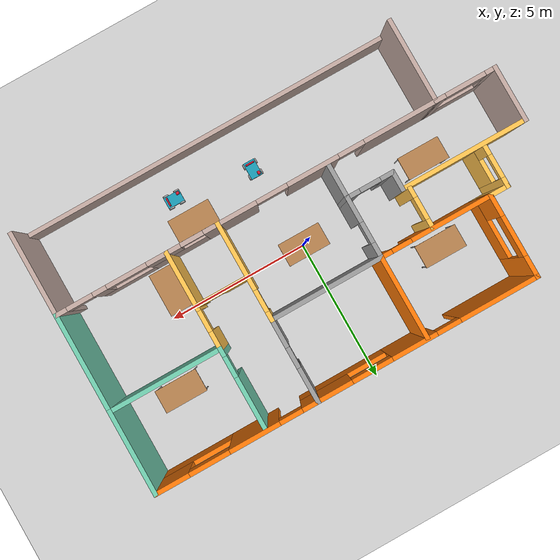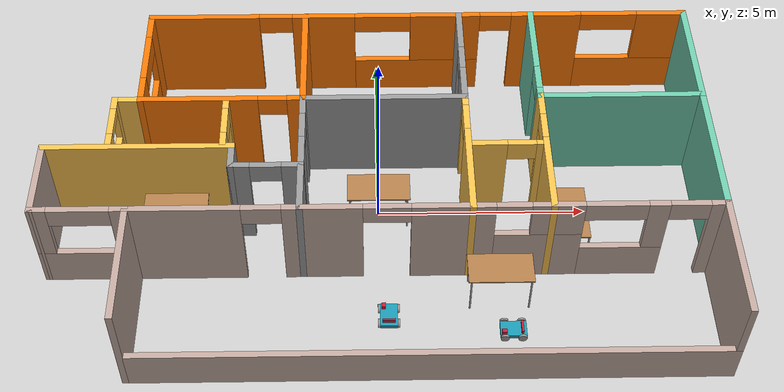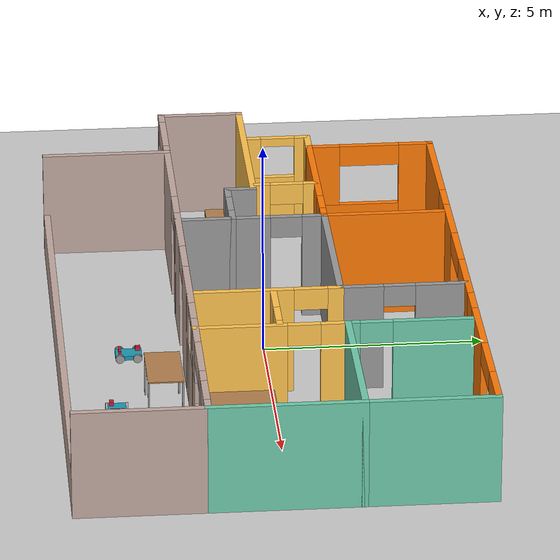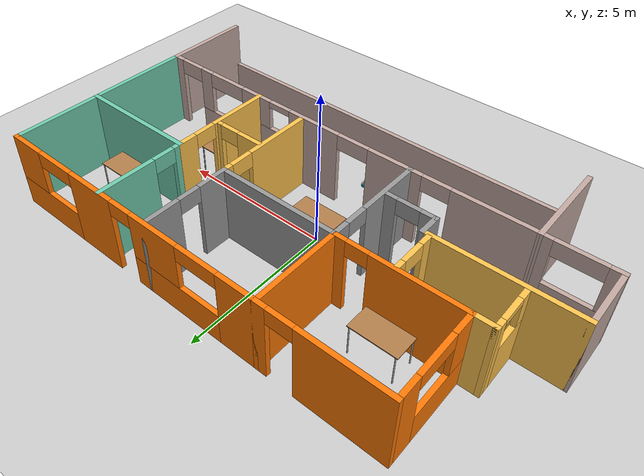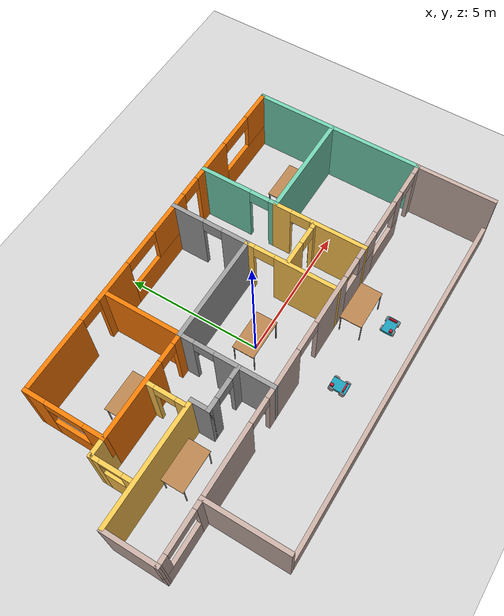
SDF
<sdf version="1.7">
 <world name="__default__">
  <plugin name="welcome" filename="libwelcome.so"/>
  <gravity>0 0 -9.8</gravity>
  <magnetic_field>6e-06 2.3e-05 -4.2e-05</magnetic_field>
  <atmosphere type="adiabatic"/>
  <physics type="ode">
   <max_step_size>0.001</max_step_size>
   <real_time_factor>1</real_time_factor>
   <real_time_update_rate>1000</real_time_update_rate>
  </physics>
  <scene><ambient>0.4 0.4 0.4 1</ambient><background>0.7 0.7 0.7 1</background><shadows>1</shadows></scene>
  <spherical_coordinates>
   <surface_model>EARTH_WGS84</surface_model>
   <latitude_deg>0</latitude_deg>
   <longitude_deg>0</longitude_deg>
   <elevation>0</elevation>
   <heading_deg>0</heading_deg>
  </spherical_coordinates>
  <model name="Building">
   <link name="Wall_0">
    <pose>1.05011 4.39635 0 0 -0 0</pose>
    <visual name="Wall_0_Visual_0">
     <pose>-5.36603 0 1.25 0 -0 0</pose>
     <geometry><box><size>2.76795 0.15 2.5</size></box></geometry>
     <material>
      <script><uri>file://media/materials/scripts/gazebo.material</uri><name>Gazebo/Grey</name></script>
      <ambient>0.996078 0.47451 0.0196078 1</ambient>
     </material>
     <meta><layer>0</layer></meta>
    </visual>
    <collision name="Wall_0_Collision_0">
     <geometry><box><size>2.76795 0.15 2.5</size></box></geometry>
     <pose>-5.36603 0 1.25 0 -0 0</pose>
    </collision>
    <visual name="Wall_0_Visual_1">
     <pose>-2.37459 0 1.25 0 -0 0</pose>
     <geometry><box><size>1.56929 0.15 2.5</size></box></geometry>
     <material>
      <script><uri>file://media/materials/scripts/gazebo.material</uri><name>Gazebo/Grey</name></script>
      <ambient>0.996078 0.47451 0.0196078 1</ambient>
     </material>
     <meta><layer>0</layer></meta>
    </visual>
    <collision name="Wall_0_Collision_1">
     <geometry><box><size>1.56929 0.15 2.5</size></box></geometry>
     <pose>-2.37459 0 1.25 0 -0 0</pose>
    </collision>
    <visual name="Wall_0_Visual_2">
     <pose>3.2233 0 1.25 0 -0 0</pose>
     <geometry><box><size>1.75312 0.15 2.5</size></box></geometry>
     <material>
      <script><uri>file://media/materials/scripts/gazebo.material</uri><name>Gazebo/Grey</name></script>
      <ambient>0.996078 0.47451 0.0196078 1</ambient>
     </material>
     <meta><layer>0</layer></meta>
    </visual>
    <collision name="Wall_0_Collision_2">
     <geometry><box><size>1.75312 0.15 2.5</size></box></geometry>
     <pose>3.2233 0 1.25 0 -0 0</pose>
    </collision>
    <visual name="Wall_0_Visual_3">
     <pose>-0.015857 0 0.5 0 -0 0</pose>
     <geometry><box><size>3.14818 0.15 1</size></box></geometry>
     <material>
      <script><uri>file://media/materials/scripts/gazebo.material</uri><name>Gazebo/Grey</name></script>
      <ambient>0.996078 0.47451 0.0196078 1</ambient>
     </material>
     <meta><layer>0</layer></meta>
    </visual>
    <collision name="Wall_0_Collision_3">
     <geometry><box><size>3.14818 0.15 1</size></box></geometry>
     <pose>-0.015857 0 0.5 0 -0 0</pose>
    </collision>
    <visual name="Wall_0_Visual_4">
     <pose>5.42493 0 0.5 0 -0 0</pose>
     <geometry><box><size>2.65014 0.15 1</size></box></geometry>
     <material>
      <script><uri>file://media/materials/scripts/gazebo.material</uri><name>Gazebo/Grey</name></script>
      <ambient>0.996078 0.47451 0.0196078 1</ambient>
     </material>
     <meta><layer>0</layer></meta>
    </visual>
    <collision name="Wall_0_Collision_4">
     <geometry><box><size>2.65014 0.15 1</size></box></geometry>
     <pose>5.42493 0 0.5 0 -0 0</pose>
    </collision>
    <visual name="Wall_0_Visual_5">
     <pose>0.684143 0 1.75 0 -0 0</pose>
     <geometry><box><size>1.74818 0.15 1.5</size></box></geometry>
     <material>
      <script><uri>file://media/materials/scripts/gazebo.material</uri><name>Gazebo/Grey</name></script>
      <ambient>0.996078 0.47451 0.0196078 1</ambient>
     </material>
     <meta><layer>0</layer></meta>
    </visual>
    <collision name="Wall_0_Collision_5">
     <geometry><box><size>1.74818 0.15 1.5</size></box></geometry>
     <pose>0.684143 0 1.75 0 -0 0</pose>
    </collision>
    <visual name="Wall_0_Visual_6">
     <pose>0.684143 0 1.75 0 -0 0</pose>
     <geometry><box><size>1.74818 0.15 1.5</size></box></geometry>
     <material>
      <script><uri>file://media/materials/scripts/gazebo.material</uri><name>Gazebo/Grey</name></script>
      <ambient>0.996078 0.47451 0.0196078 1</ambient>
     </material>
     <meta><layer>0</layer></meta>
    </visual>
    <collision name="Wall_0_Collision_6">
     <geometry><box><size>1.74818 0.15 1.5</size></box></geometry>
     <pose>0.684143 0 1.75 0 -0 0</pose>
    </collision>
    <visual name="Wall_0_Visual_7">
     <pose>6.12493 0 1.75 0 -0 0</pose>
     <geometry><box><size>1.25014 0.15 1.5</size></box></geometry>
     <material>
      <script><uri>file://media/materials/scripts/gazebo.material</uri><name>Gazebo/Grey</name></script>
      <ambient>0.996078 0.47451 0.0196078 1</ambient>
     </material>
     <meta><layer>0</layer></meta>
    </visual>
    <collision name="Wall_0_Collision_7">
     <geometry><box><size>1.25014 0.15 1.5</size></box></geometry>
     <pose>6.12493 0 1.75 0 -0 0</pose>
    </collision>
    <visual name="Wall_0_Visual_8">
     <pose>-3.57065 0 2.25 0 -0 0</pose>
     <geometry><box><size>0.822813 0.15 0.5</size></box></geometry>
     <material>
      <script><uri>file://media/materials/scripts/gazebo.material</uri><name>Gazebo/Grey</name></script>
      <ambient>0.996078 0.47451 0.0196078 1</ambient>
     </material>
     <meta><layer>0</layer></meta>
    </visual>
    <collision name="Wall_0_Collision_8">
     <geometry><box><size>0.822813 0.15 0.5</size></box></geometry>
     <pose>-3.57065 0 2.25 0 -0 0</pose>
    </collision>
    <visual name="Wall_0_Visual_9">
     <pose>-0.889948 0 2.25 0 -0 0</pose>
     <geometry><box><size>1.4 0.15 0.5</size></box></geometry>
     <material>
      <script><uri>file://media/materials/scripts/gazebo.material</uri><name>Gazebo/Grey</name></script>
      <ambient>0.996078 0.47451 0.0196078 1</ambient>
     </material>
     <meta><layer>0</layer></meta>
    </visual>
    <collision name="Wall_0_Collision_9">
     <geometry><box><size>1.4 0.15 0.5</size></box></geometry>
     <pose>-0.889948 0 2.25 0 -0 0</pose>
    </collision>
    <visual name="Wall_0_Visual_10">
     <pose>4.79986 0 2.25 0 -0 0</pose>
     <geometry><box><size>1.4 0.15 0.5</size></box></geometry>
     <material>
      <script><uri>file://media/materials/scripts/gazebo.material</uri><name>Gazebo/Grey</name></script>
      <ambient>0.996078 0.47451 0.0196078 1</ambient>
     </material>
     <meta><layer>0</layer></meta>
    </visual>
    <collision name="Wall_0_Collision_10">
     <geometry><box><size>1.4 0.15 0.5</size></box></geometry>
     <pose>4.79986 0 2.25 0 -0 0</pose>
    </collision>
    <visual name="Wall_0_Visual_11">
     <pose>1.95249 0 2.25 0 -0 0</pose>
     <geometry><box><size>0.788508 0.15 0.5</size></box></geometry>
     <material>
      <script><uri>file://media/materials/scripts/gazebo.material</uri><name>Gazebo/Grey</name></script>
      <ambient>0.996078 0.47451 0.0196078 1</ambient>
     </material>
     <meta><layer>0</layer></meta>
    </visual>
    <collision name="Wall_0_Collision_11">
     <geometry><box><size>0.788508 0.15 0.5</size></box></geometry>
     <pose>1.95249 0 2.25 0 -0 0</pose>
    </collision>
    <visual name="Wall_0_Visual_12">
     <pose>1.95249 0 2.25 0 -0 0</pose>
     <geometry><box><size>0.788508 0.15 0.5</size></box></geometry>
     <material>
      <script><uri>file://media/materials/scripts/gazebo.material</uri><name>Gazebo/Grey</name></script>
      <ambient>0.996078 0.47451 0.0196078 1</ambient>
     </material>
     <meta><layer>0</layer></meta>
    </visual>
    <collision name="Wall_0_Collision_12">
     <geometry><box><size>0.788508 0.15 0.5</size></box></geometry>
     <pose>1.95249 0 2.25 0 -0 0</pose>
    </collision>
   </link>
   <link name="Wall_10">
    <collision name="Wall_10_Collision">
     <geometry><box><size>4 0.15 2.5</size></box></geometry>
     <pose>0 0 1.25 0 -0 0</pose>
    </collision>
    <visual name="Wall_10_Visual">
     <pose>0 0 1.25 0 -0 0</pose>
     <geometry><box><size>4 0.15 2.5</size></box></geometry>
     <material>
      <script><uri>file://media/materials/scripts/gazebo.material</uri><name>Gazebo/Grey</name></script>
      <ambient>1 1 1 1</ambient>
     </material>
     <meta><layer>0</layer></meta>
    </visual>
    <pose>0.150112 1.54635 0 0 -0 0</pose>
   </link>
   <link name="Wall_107">
    <pose>2.07511 -0.128649 0 0 -0 -1.5708</pose>
    <visual name="Wall_107_Visual_0">
     <pose>-1.57211 0 1.25 0 -0 0</pose>
     <geometry><box><size>0.355782 0.15 2.5</size></box></geometry>
     <material>
      <script><uri>file://media/materials/scripts/gazebo.material</uri><name>Gazebo/Grey</name></script>
      <ambient>1 0.764706 0.305882 1</ambient>
     </material>
     <meta><layer>0</layer></meta>
    </visual>
    <collision name="Wall_107_Collision_0">
     <geometry><box><size>0.355782 0.15 2.5</size></box></geometry>
     <pose>-1.57211 0 1.25 0 -0 0</pose>
    </collision>
    <visual name="Wall_107_Visual_1">
     <pose>0.556557 0 1.25 0 -0 0</pose>
     <geometry><box><size>2.38689 0.15 2.5</size></box></geometry>
     <material>
      <script><uri>file://media/materials/scripts/gazebo.material</uri><name>Gazebo/Grey</name></script>
      <ambient>1 0.764706 0.305882 1</ambient>
     </material>
     <meta><layer>0</layer></meta>
    </visual>
    <collision name="Wall_107_Collision_1">
     <geometry><box><size>2.38689 0.15 2.5</size></box></geometry>
     <pose>0.556557 0 1.25 0 -0 0</pose>
    </collision>
    <visual name="Wall_107_Visual_2">
     <pose>-1.01555 0 2.25 0 -0 0</pose>
     <geometry><box><size>0.757332 0.15 0.5</size></box></geometry>
     <material>
      <script><uri>file://media/materials/scripts/gazebo.material</uri><name>Gazebo/Grey</name></script>
      <ambient>1 0.764706 0.305882 1</ambient>
     </material>
     <meta><layer>0</layer></meta>
    </visual>
    <collision name="Wall_107_Collision_2">
     <geometry><box><size>0.757332 0.15 0.5</size></box></geometry>
     <pose>-1.01555 0 2.25 0 -0 0</pose>
    </collision>
   </link>
   <link name="Wall_11">
    <pose>2.07511 2.97135 0 0 -0 1.5708</pose>
    <visual name="Wall_11_Visual_0">
     <pose>-0.979075 0 1.25 0 -0 0</pose>
     <geometry><box><size>1.04185 0.15 2.5</size></box></geometry>
     <material>
      <script><uri>file://media/materials/scripts/gazebo.material</uri><name>Gazebo/Grey</name></script>
      <ambient>1 1 1 1</ambient>
     </material>
     <meta><layer>0</layer></meta>
    </visual>
    <collision name="Wall_11_Collision_0">
     <geometry><box><size>1.04185 0.15 2.5</size></box></geometry>
     <pose>-0.979075 0 1.25 0 -0 0</pose>
    </collision>
    <visual name="Wall_11_Visual_1">
     <pose>0.87636 0 1.25 0 -0 0</pose>
     <geometry><box><size>1.24728 0.15 2.5</size></box></geometry>
     <material>
      <script><uri>file://media/materials/scripts/gazebo.material</uri><name>Gazebo/Grey</name></script>
      <ambient>1 1 1 1</ambient>
     </material>
     <meta><layer>0</layer></meta>
    </visual>
    <collision name="Wall_11_Collision_1">
     <geometry><box><size>1.24728 0.15 2.5</size></box></geometry>
     <pose>0.87636 0 1.25 0 -0 0</pose>
    </collision>
    <visual name="Wall_11_Visual_2">
     <pose>-0.102714 0 2.25 0 -0 0</pose>
     <geometry><box><size>0.71087 0.15 0.5</size></box></geometry>
     <material>
      <script><uri>file://media/materials/scripts/gazebo.material</uri><name>Gazebo/Grey</name></script>
      <ambient>1 1 1 1</ambient>
     </material>
     <meta><layer>0</layer></meta>
    </visual>
    <collision name="Wall_11_Collision_2">
     <geometry><box><size>0.71087 0.15 0.5</size></box></geometry>
     <pose>-0.102714 0 2.25 0 -0 0</pose>
    </collision>
   </link>
   <link name="Wall_115">
    <pose>2.98021 0.049674 0 0 -0 3.14159</pose>
    <visual name="Wall_115_Visual_0">
     <pose>-0.770795 0 1.25 0 -0 0</pose>
     <geometry><box><size>0.20841 0.15 2.5</size></box></geometry>
     <material>
      <script><uri>file://media/materials/scripts/gazebo.material</uri><name>Gazebo/Grey</name></script>
      <ambient>1 0.764706 0.305882 1</ambient>
     </material>
     <meta><layer>0</layer></meta>
    </visual>
    <collision name="Wall_115_Collision_0">
     <geometry><box><size>0.20841 0.15 2.5</size></box></geometry>
     <pose>-0.770795 0 1.25 0 -0 0</pose>
    </collision>
    <visual name="Wall_115_Visual_1">
     <pose>0.438613 0 1.25 0 -0 0</pose>
     <geometry><box><size>0.872773 0.15 2.5</size></box></geometry>
     <material>
      <script><uri>file://media/materials/scripts/gazebo.material</uri><name>Gazebo/Grey</name></script>
      <ambient>1 0.764706 0.305882 1</ambient>
     </material>
     <meta><layer>0</layer></meta>
    </visual>
    <collision name="Wall_115_Collision_1">
     <geometry><box><size>0.872773 0.15 2.5</size></box></geometry>
     <pose>0.438613 0 1.25 0 -0 0</pose>
    </collision>
    <visual name="Wall_115_Visual_2">
     <pose>-0.332182 0 2.25 0 -0 0</pose>
     <geometry><box><size>0.668817 0.15 0.5</size></box></geometry>
     <material>
      <script><uri>file://media/materials/scripts/gazebo.material</uri><name>Gazebo/Grey</name></script>
      <ambient>1 0.764706 0.305882 1</ambient>
     </material>
     <meta><layer>0</layer></meta>
    </visual>
    <collision name="Wall_115_Collision_2">
     <geometry><box><size>0.668817 0.15 0.5</size></box></geometry>
     <pose>-0.332182 0 2.25 0 -0 0</pose>
    </collision>
   </link>
   <link name="Wall_118">
    <collision name="Wall_118_Collision">
     <geometry><box><size>3 0.15 2.5</size></box></geometry>
     <pose>0 0 1.25 0 -0 0</pose>
    </collision>
    <visual name="Wall_118_Visual">
     <pose>0 0 1.25 0 -0 0</pose>
     <geometry><box><size>3 0.15 2.5</size></box></geometry>
     <material>
      <script><uri>file://media/materials/scripts/gazebo.material</uri><name>Gazebo/Grey</name></script>
      <ambient>0.760784 0.662745 0.627451 1</ambient>
     </material>
     <meta><layer>0</layer></meta>
    </visual>
    <pose>7.72489 -3.2285 0 0 -0 -1.57064</pose>
   </link>
   <link name="Wall_120">
    <collision name="Wall_120_Collision">
     <geometry><box><size>3 0.15 2.5</size></box></geometry>
     <pose>0 0 1.25 0 -0 0</pose>
    </collision>
    <visual name="Wall_120_Visual">
     <pose>0 0 1.25 0 -0 0</pose>
     <geometry><box><size>3 0.15 2.5</size></box></geometry>
     <material>
      <script><uri>file://media/materials/scripts/gazebo.material</uri><name>Gazebo/Grey</name></script>
      <ambient>0.760784 0.662745 0.627451 1</ambient>
     </material>
     <meta><layer>0</layer></meta>
    </visual>
    <pose>-5.62534 -3.22835 0 0 -0 -1.5708</pose>
   </link>
   <link name="Wall_122">
    <collision name="Wall_122_Collision">
     <geometry><box><size>13.5 0.15 1</size></box></geometry>
     <pose>0 0 0.5 0 -0 0</pose>
    </collision>
    <visual name="Wall_122_Visual">
     <pose>0 0 0.5 0 -0 0</pose>
     <geometry><box><size>13.5 0.15 1</size></box></geometry>
     <material>
      <script><uri>file://media/materials/scripts/gazebo.material</uri><name>Gazebo/Grey</name></script>
      <ambient>0.760784 0.662745 0.627451 1</ambient>
     </material>
     <meta><layer>0</layer></meta>
    </visual>
    <pose>1.04989 -4.6535 0 0 -0 -2.3e-05</pose>
   </link>
   <link name="Wall_136">
    <collision name="Wall_136_Collision">
     <geometry><box><size>0.75 0.15 2.5</size></box></geometry>
     <pose>0 0 1.25 0 -0 0</pose>
    </collision>
    <visual name="Wall_136_Visual">
     <pose>0 0 1.25 0 -0 0</pose>
     <geometry><box><size>0.75 0.15 2.5</size></box></geometry>
     <material>
      <script><uri>file://media/materials/scripts/gazebo.material</uri><name>Gazebo/Grey</name></script>
      <ambient>1 0.764706 0.305882 1</ambient>
     </material>
     <meta><layer>0</layer></meta>
    </visual>
    <pose>-5.92489 1.54635 0 0 -0 3.14159</pose>
   </link>
   <link name="Wall_137">
    <pose>-6.22489 0.871351 0 0 -0 -1.5708</pose>
    <visual name="Wall_137_Visual_0">
     <pose>-0.5638 0 1.25 0 -0 0</pose>
     <geometry><box><size>0.3724 0.15 2.5</size></box></geometry>
     <material>
      <script><uri>file://media/materials/scripts/gazebo.material</uri><name>Gazebo/Grey</name></script>
      <ambient>1 0.764706 0.305882 1</ambient>
     </material>
     <meta><layer>0</layer></meta>
    </visual>
    <collision name="Wall_137_Collision_0">
     <geometry><box><size>0.3724 0.15 2.5</size></box></geometry>
     <pose>-0.5638 0 1.25 0 -0 0</pose>
    </collision>
    <visual name="Wall_137_Visual_1">
     <pose>0.1862 0 0.75 0 -0 0</pose>
     <geometry><box><size>1.1276 0.15 1.5</size></box></geometry>
     <material>
      <script><uri>file://media/materials/scripts/gazebo.material</uri><name>Gazebo/Grey</name></script>
      <ambient>1 0.764706 0.305882 1</ambient>
     </material>
     <meta><layer>0</layer></meta>
    </visual>
    <collision name="Wall_137_Collision_1">
     <geometry><box><size>1.1276 0.15 1.5</size></box></geometry>
     <pose>0.1862 0 0.75 0 -0 0</pose>
    </collision>
    <visual name="Wall_137_Visual_2">
     <pose>0.5862 0 2 0 -0 0</pose>
     <geometry><box><size>0.3276 0.15 1</size></box></geometry>
     <material>
      <script><uri>file://media/materials/scripts/gazebo.material</uri><name>Gazebo/Grey</name></script>
      <ambient>1 0.764706 0.305882 1</ambient>
     </material>
     <meta><layer>0</layer></meta>
    </visual>
    <collision name="Wall_137_Collision_2">
     <geometry><box><size>0.3276 0.15 1</size></box></geometry>
     <pose>0.5862 0 2 0 -0 0</pose>
    </collision>
    <visual name="Wall_137_Visual_3">
     <pose>0.0224 0 2.4 0 -0 0</pose>
     <geometry><box><size>0.8 0.15 0.2</size></box></geometry>
     <material>
      <script><uri>file://media/materials/scripts/gazebo.material</uri><name>Gazebo/Grey</name></script>
      <ambient>1 0.764706 0.305882 1</ambient>
     </material>
     <meta><layer>0</layer></meta>
    </visual>
    <collision name="Wall_137_Collision_3">
     <geometry><box><size>0.8 0.15 0.2</size></box></geometry>
     <pose>0.0224 0 2.4 0 -0 0</pose>
    </collision>
   </link>
   <link name="Wall_139">
    <pose>-3.58813 0.821217 0 0 -0 -1.5708</pose>
    <visual name="Wall_139_Visual_0">
     <pose>-0.574639 0 1.25 0 -0 0</pose>
     <geometry><box><size>0.350722 0.15 2.5</size></box></geometry>
     <material>
      <script><uri>file://media/materials/scripts/gazebo.material</uri><name>Gazebo/Grey</name></script>
      <ambient>1 0.764706 0.305882 1</ambient>
     </material>
     <meta><layer>0</layer></meta>
    </visual>
    <collision name="Wall_139_Collision_0">
     <geometry><box><size>0.350722 0.15 2.5</size></box></geometry>
     <pose>-0.574639 0 1.25 0 -0 0</pose>
    </collision>
    <visual name="Wall_139_Visual_1">
     <pose>0.556712 0 1.25 0 -0 0</pose>
     <geometry><box><size>0.386577 0.15 2.5</size></box></geometry>
     <material>
      <script><uri>file://media/materials/scripts/gazebo.material</uri><name>Gazebo/Grey</name></script>
      <ambient>1 0.764706 0.305882 1</ambient>
     </material>
     <meta><layer>0</layer></meta>
    </visual>
    <collision name="Wall_139_Collision_1">
     <geometry><box><size>0.386577 0.15 2.5</size></box></geometry>
     <pose>0.556712 0 1.25 0 -0 0</pose>
    </collision>
    <visual name="Wall_139_Visual_2">
     <pose>-0.017927 0 2.25 0 -0 0</pose>
     <geometry><box><size>0.762701 0.15 0.5</size></box></geometry>
     <material>
      <script><uri>file://media/materials/scripts/gazebo.material</uri><name>Gazebo/Grey</name></script>
      <ambient>1 0.764706 0.305882 1</ambient>
     </material>
     <meta><layer>0</layer></meta>
    </visual>
    <collision name="Wall_139_Collision_2">
     <geometry><box><size>0.762701 0.15 0.5</size></box></geometry>
     <pose>-0.017927 0 2.25 0 -0 0</pose>
    </collision>
   </link>
   <link name="Wall_143">
    <pose>-2.57489 -0.553649 0 0 -0 0</pose>
    <visual name="Wall_143_Visual_0">
     <pose>-0.619924 0 1.25 0 -0 0</pose>
     <geometry><box><size>0.510151 0.15 2.5</size></box></geometry>
     <material>
      <script><uri>file://media/materials/scripts/gazebo.material</uri><name>Gazebo/Grey</name></script>
      <ambient>1 1 1 1</ambient>
     </material>
     <meta><layer>0</layer></meta>
    </visual>
    <collision name="Wall_143_Collision_0">
     <geometry><box><size>0.510151 0.15 2.5</size></box></geometry>
     <pose>-0.619924 0 1.25 0 -0 0</pose>
    </collision>
    <visual name="Wall_143_Visual_1">
     <pose>0.616812 0 1.25 0 -0 0</pose>
     <geometry><box><size>0.516376 0.15 2.5</size></box></geometry>
     <material>
      <script><uri>file://media/materials/scripts/gazebo.material</uri><name>Gazebo/Grey</name></script>
      <ambient>1 1 1 1</ambient>
     </material>
     <meta><layer>0</layer></meta>
    </visual>
    <collision name="Wall_143_Collision_1">
     <geometry><box><size>0.516376 0.15 2.5</size></box></geometry>
     <pose>0.616812 0 1.25 0 -0 0</pose>
    </collision>
    <visual name="Wall_143_Visual_2">
     <pose>-0.003112 0 2.25 0 -0 0</pose>
     <geometry><box><size>0.723473 0.15 0.5</size></box></geometry>
     <material>
      <script><uri>file://media/materials/scripts/gazebo.material</uri><name>Gazebo/Grey</name></script>
      <ambient>1 1 1 1</ambient>
     </material>
     <meta><layer>0</layer></meta>
    </visual>
    <collision name="Wall_143_Collision_2">
     <geometry><box><size>0.723473 0.15 0.5</size></box></geometry>
     <pose>-0.003112 0 2.25 0 -0 0</pose>
    </collision>
   </link>
   <link name="Wall_145">
    <pose>-6.67511 -1.8035 0 0 -0 -3.14145</pose>
    <visual name="Wall_145_Visual_0">
     <pose>-0.916173 0 1.25 0 -0 0</pose>
     <geometry><box><size>0.417655 0.15 2.5</size></box></geometry>
     <material>
      <script><uri>file://media/materials/scripts/gazebo.material</uri><name>Gazebo/Grey</name></script>
      <ambient>0.760784 0.662745 0.627451 1</ambient>
     </material>
     <meta><layer>0</layer></meta>
    </visual>
    <collision name="Wall_145_Collision_0">
     <geometry><box><size>0.417655 0.15 2.5</size></box></geometry>
     <pose>-0.916173 0 1.25 0 -0 0</pose>
    </collision>
    <visual name="Wall_145_Visual_1">
     <pose>0.208827 0 0.5 0 -0 0</pose>
     <geometry><box><size>1.83234 0.15 1</size></box></geometry>
     <material>
      <script><uri>file://media/materials/scripts/gazebo.material</uri><name>Gazebo/Grey</name></script>
      <ambient>0.760784 0.662745 0.627451 1</ambient>
     </material>
     <meta><layer>0</layer></meta>
    </visual>
    <collision name="Wall_145_Collision_1">
     <geometry><box><size>1.83234 0.15 1</size></box></geometry>
     <pose>0.208827 0 0.5 0 -0 0</pose>
    </collision>
    <visual name="Wall_145_Visual_2">
     <pose>0.908827 0 1.75 0 -0 0</pose>
     <geometry><box><size>0.432345 0.15 1.5</size></box></geometry>
     <material>
      <script><uri>file://media/materials/scripts/gazebo.material</uri><name>Gazebo/Grey</name></script>
      <ambient>0.760784 0.662745 0.627451 1</ambient>
     </material>
     <meta><layer>0</layer></meta>
    </visual>
    <collision name="Wall_145_Collision_2">
     <geometry><box><size>0.432345 0.15 1.5</size></box></geometry>
     <pose>0.908827 0 1.75 0 -0 0</pose>
    </collision>
    <visual name="Wall_145_Visual_3">
     <pose>-0.007345 0 2.25 0 -0 0</pose>
     <geometry><box><size>1.4 0.15 0.5</size></box></geometry>
     <material>
      <script><uri>file://media/materials/scripts/gazebo.material</uri><name>Gazebo/Grey</name></script>
      <ambient>0.760784 0.662745 0.627451 1</ambient>
     </material>
     <meta><layer>0</layer></meta>
    </visual>
    <collision name="Wall_145_Collision_3">
     <geometry><box><size>1.4 0.15 0.5</size></box></geometry>
     <pose>-0.007345 0 2.25 0 -0 0</pose>
    </collision>
   </link>
   <link name="Wall_146">
    <collision name="Wall_146_Collision">
     <geometry><box><size>2 0.15 2.5</size></box></geometry>
     <pose>0 0 1.25 0 -0 0</pose>
    </collision>
    <visual name="Wall_146_Visual">
     <pose>0 0 1.25 0 -0 0</pose>
     <geometry><box><size>2 0.15 2.5</size></box></geometry>
     <material>
      <script><uri>file://media/materials/scripts/gazebo.material</uri><name>Gazebo/Grey</name></script>
      <ambient>0.760784 0.662745 0.627451 1</ambient>
     </material>
     <meta><layer>0</layer></meta>
    </visual>
    <pose>-7.72489 -0.878649 0 0 -0 1.5708</pose>
   </link>
   <link name="Wall_147">
    <collision name="Wall_147_Collision">
     <geometry><box><size>4.5 0.15 2.5</size></box></geometry>
     <pose>0 0 1.25 0 -0 0</pose>
    </collision>
    <visual name="Wall_147_Visual">
     <pose>0 0 1.25 0 -0 0</pose>
     <geometry><box><size>4.5 0.15 2.5</size></box></geometry>
     <material>
      <script><uri>file://media/materials/scripts/gazebo.material</uri><name>Gazebo/Grey</name></script>
      <ambient>1 0.764706 0.305882 1</ambient>
     </material>
     <meta><layer>0</layer></meta>
    </visual>
    <pose>-5.54989 0.046351 0 0 -0 0</pose>
   </link>
   <link name="Wall_148">
    <collision name="Wall_148_Collision">
     <geometry><box><size>0.75 0.15 2.5</size></box></geometry>
     <pose>0 0 1.25 0 -0 0</pose>
    </collision>
    <visual name="Wall_148_Visual">
     <pose>0 0 1.25 0 -0 0</pose>
     <geometry><box><size>0.75 0.15 2.5</size></box></geometry>
     <material>
      <script><uri>file://media/materials/scripts/gazebo.material</uri><name>Gazebo/Grey</name></script>
      <ambient>1 1 1 1</ambient>
     </material>
     <meta><layer>0</layer></meta>
    </visual>
    <pose>-3.37489 -0.253649 0 0 -0 -1.5708</pose>
   </link>
   <link name="Wall_2">
    <collision name="Wall_2_Collision">
     <geometry><box><size>3 0.15 2.5</size></box></geometry>
     <pose>0 0 1.25 0 -0 0</pose>
    </collision>
    <visual name="Wall_2_Visual">
     <pose>0 0 1.25 0 -0 0</pose>
     <geometry><box><size>3 0.15 2.5</size></box></geometry>
     <material>
      <script><uri>file://media/materials/scripts/gazebo.material</uri><name>Gazebo/Grey</name></script>
      <ambient>0.435294 0.796078 0.67451 1</ambient>
     </material>
     <meta><layer>0</layer></meta>
    </visual>
    <pose>7.72511 2.97135 0 0 -0 -1.5708</pose>
   </link>
   <link name="Wall_25">
    <collision name="Wall_25_Collision">
     <geometry><box><size>3.5 0.15 2.5</size></box></geometry>
     <pose>0 0 1.25 0 -0 0</pose>
    </collision>
    <visual name="Wall_25_Visual">
     <pose>0 0 1.25 0 -0 0</pose>
     <geometry><box><size>3.5 0.15 2.5</size></box></geometry>
     <material>
      <script><uri>file://media/materials/scripts/gazebo.material</uri><name>Gazebo/Grey</name></script>
      <ambient>0.435294 0.796078 0.67451 1</ambient>
     </material>
     <meta><layer>0</layer></meta>
    </visual>
    <pose>7.72489 -0.128499 0 0 -0 -1.57093</pose>
   </link>
   <link name="Wall_27">
    <pose>3.87511 -0.128649 0 0 -0 1.5708</pose>
    <visual name="Wall_27_Visual_0">
     <pose>-0.703233 0 1.25 0 -0 0</pose>
     <geometry><box><size>2.09354 0.15 2.5</size></box></geometry>
     <material>
      <script><uri>file://media/materials/scripts/gazebo.material</uri><name>Gazebo/Grey</name></script>
      <ambient>1 0.764706 0.305882 1</ambient>
     </material>
     <meta><layer>0</layer></meta>
    </visual>
    <collision name="Wall_27_Collision_0">
     <geometry><box><size>2.09354 0.15 2.5</size></box></geometry>
     <pose>-0.703233 0 1.25 0 -0 0</pose>
    </collision>
    <visual name="Wall_27_Visual_1">
     <pose>1.41102 0 1.25 0 -0 0</pose>
     <geometry><box><size>0.677954 0.15 2.5</size></box></geometry>
     <material>
      <script><uri>file://media/materials/scripts/gazebo.material</uri><name>Gazebo/Grey</name></script>
      <ambient>1 0.764706 0.305882 1</ambient>
     </material>
     <meta><layer>0</layer></meta>
    </visual>
    <collision name="Wall_27_Collision_1">
     <geometry><box><size>0.677954 0.15 2.5</size></box></geometry>
     <pose>1.41102 0 1.25 0 -0 0</pose>
    </collision>
    <visual name="Wall_27_Visual_2">
     <pose>0.70779 0 2.25 0 -0 0</pose>
     <geometry><box><size>0.728512 0.15 0.5</size></box></geometry>
     <material>
      <script><uri>file://media/materials/scripts/gazebo.material</uri><name>Gazebo/Grey</name></script>
      <ambient>1 0.764706 0.305882 1</ambient>
     </material>
     <meta><layer>0</layer></meta>
    </visual>
    <collision name="Wall_27_Collision_2">
     <geometry><box><size>0.728512 0.15 0.5</size></box></geometry>
     <pose>0.70779 0 2.25 0 -0 0</pose>
    </collision>
   </link>
   <link name="Wall_3">
    <collision name="Wall_3_Collision">
     <geometry><box><size>4 0.15 2.5</size></box></geometry>
     <pose>0 0 1.25 0 -0 0</pose>
    </collision>
    <visual name="Wall_3_Visual">
     <pose>0 0 1.25 0 -0 0</pose>
     <geometry><box><size>4 0.15 2.5</size></box></geometry>
     <material>
      <script><uri>file://media/materials/scripts/gazebo.material</uri><name>Gazebo/Grey</name></script>
      <ambient>0.435294 0.796078 0.67451 1</ambient>
     </material>
     <meta><layer>0</layer></meta>
    </visual>
    <pose>5.80011 1.54635 0 0 -0 3.14159</pose>
   </link>
   <link name="Wall_4">
    <pose>3.87511 2.97135 0 0 -0 1.5708</pose>
    <visual name="Wall_4_Visual_0">
     <pose>-1.33125 0 1.25 0 -0 0</pose>
     <geometry><box><size>0.337503 0.15 2.5</size></box></geometry>
     <material>
      <script><uri>file://media/materials/scripts/gazebo.material</uri><name>Gazebo/Grey</name></script>
      <ambient>0.435294 0.796078 0.67451 1</ambient>
     </material>
     <meta><layer>0</layer></meta>
    </visual>
    <collision name="Wall_4_Collision_0">
     <geometry><box><size>0.337503 0.15 2.5</size></box></geometry>
     <pose>-1.33125 0 1.25 0 -0 0</pose>
    </collision>
    <visual name="Wall_4_Visual_1">
     <pose>0.530708 0 1.25 0 -0 0</pose>
     <geometry><box><size>1.93858 0.15 2.5</size></box></geometry>
     <material>
      <script><uri>file://media/materials/scripts/gazebo.material</uri><name>Gazebo/Grey</name></script>
      <ambient>0.435294 0.796078 0.67451 1</ambient>
     </material>
     <meta><layer>0</layer></meta>
    </visual>
    <collision name="Wall_4_Collision_1">
     <geometry><box><size>1.93858 0.15 2.5</size></box></geometry>
     <pose>0.530708 0 1.25 0 -0 0</pose>
    </collision>
    <visual name="Wall_4_Visual_2">
     <pose>-0.80054 0 2.25 0 -0 0</pose>
     <geometry><box><size>0.723913 0.15 0.5</size></box></geometry>
     <material>
      <script><uri>file://media/materials/scripts/gazebo.material</uri><name>Gazebo/Grey</name></script>
      <ambient>0.435294 0.796078 0.67451 1</ambient>
     </material>
     <meta><layer>0</layer></meta>
    </visual>
    <collision name="Wall_4_Collision_2">
     <geometry><box><size>0.723913 0.15 0.5</size></box></geometry>
     <pose>-0.80054 0 2.25 0 -0 0</pose>
    </collision>
   </link>
   <link name="Wall_45">
    <pose>1.04966 -1.80335 0 0 -0 0</pose>
    <visual name="Wall_45_Visual_0">
     <pose>-5.43857 0 1.25 0 -0 0</pose>
     <geometry><box><size>2.62285 0.15 2.5</size></box></geometry>
     <material>
      <script><uri>file://media/materials/scripts/gazebo.material</uri><name>Gazebo/Grey</name></script>
      <ambient>0.760784 0.662745 0.627451 1</ambient>
     </material>
     <meta><layer>0</layer></meta>
    </visual>
    <collision name="Wall_45_Collision_0">
     <geometry><box><size>2.62285 0.15 2.5</size></box></geometry>
     <pose>-5.43857 0 1.25 0 -0 0</pose>
    </collision>
    <visual name="Wall_45_Visual_1">
     <pose>-2.32325 0 1.25 0 -0 0</pose>
     <geometry><box><size>1.80779 0.15 2.5</size></box></geometry>
     <material>
      <script><uri>file://media/materials/scripts/gazebo.material</uri><name>Gazebo/Grey</name></script>
      <ambient>0.760784 0.662745 0.627451 1</ambient>
     </material>
     <meta><layer>0</layer></meta>
    </visual>
    <collision name="Wall_45_Collision_1">
     <geometry><box><size>1.80779 0.15 2.5</size></box></geometry>
     <pose>-2.32325 0 1.25 0 -0 0</pose>
    </collision>
    <visual name="Wall_45_Visual_2">
     <pose>0.602257 0 1.25 0 -0 0</pose>
     <geometry><box><size>1.88007 0.15 2.5</size></box></geometry>
     <material>
      <script><uri>file://media/materials/scripts/gazebo.material</uri><name>Gazebo/Grey</name></script>
      <ambient>0.760784 0.662745 0.627451 1</ambient>
     </material>
     <meta><layer>0</layer></meta>
    </visual>
    <collision name="Wall_45_Collision_2">
     <geometry><box><size>1.88007 0.15 2.5</size></box></geometry>
     <pose>0.602257 0 1.25 0 -0 0</pose>
    </collision>
    <visual name="Wall_45_Visual_3">
     <pose>6.52765 0 1.25 0 -0 0</pose>
     <geometry><box><size>0.444692 0.15 2.5</size></box></geometry>
     <material>
      <script><uri>file://media/materials/scripts/gazebo.material</uri><name>Gazebo/Grey</name></script>
      <ambient>0.760784 0.662745 0.627451 1</ambient>
     </material>
     <meta><layer>0</layer></meta>
    </visual>
    <collision name="Wall_45_Collision_3">
     <geometry><box><size>0.444692 0.15 2.5</size></box></geometry>
     <pose>6.52765 0 1.25 0 -0 0</pose>
    </collision>
    <visual name="Wall_45_Visual_4">
     <pose>2.53482 0 0.75 0 -0 0</pose>
     <geometry><box><size>1.98504 0.15 1.5</size></box></geometry>
     <material>
      <script><uri>file://media/materials/scripts/gazebo.material</uri><name>Gazebo/Grey</name></script>
      <ambient>0.760784 0.662745 0.627451 1</ambient>
     </material>
     <meta><layer>0</layer></meta>
    </visual>
    <collision name="Wall_45_Collision_4">
     <geometry><box><size>1.98504 0.15 1.5</size></box></geometry>
     <pose>2.53482 0 0.75 0 -0 0</pose>
    </collision>
    <visual name="Wall_45_Visual_5">
     <pose>4.46632 0 0.5 0 -0 0</pose>
     <geometry><box><size>1.87797 0.15 1</size></box></geometry>
     <material>
      <script><uri>file://media/materials/scripts/gazebo.material</uri><name>Gazebo/Grey</name></script>
      <ambient>0.760784 0.662745 0.627451 1</ambient>
     </material>
     <meta><layer>0</layer></meta>
    </visual>
    <collision name="Wall_45_Collision_5">
     <geometry><box><size>1.87797 0.15 1</size></box></geometry>
     <pose>4.46632 0 0.5 0 -0 0</pose>
    </collision>
    <visual name="Wall_45_Visual_6">
     <pose>5.16632 0 1.75 0 -0 0</pose>
     <geometry><box><size>0.477971 0.15 1.5</size></box></geometry>
     <material>
      <script><uri>file://media/materials/scripts/gazebo.material</uri><name>Gazebo/Grey</name></script>
      <ambient>0.760784 0.662745 0.627451 1</ambient>
     </material>
     <meta><layer>0</layer></meta>
    </visual>
    <collision name="Wall_45_Collision_6">
     <geometry><box><size>0.477971 0.15 1.5</size></box></geometry>
     <pose>5.16632 0 1.75 0 -0 0</pose>
    </collision>
    <visual name="Wall_45_Visual_7">
     <pose>2.93482 0 2 0 -0 0</pose>
     <geometry><box><size>1.18504 0.15 1</size></box></geometry>
     <material>
      <script><uri>file://media/materials/scripts/gazebo.material</uri><name>Gazebo/Grey</name></script>
      <ambient>0.760784 0.662745 0.627451 1</ambient>
     </material>
     <meta><layer>0</layer></meta>
    </visual>
    <collision name="Wall_45_Collision_7">
     <geometry><box><size>1.18504 0.15 1</size></box></geometry>
     <pose>2.93482 0 2 0 -0 0</pose>
    </collision>
    <visual name="Wall_45_Visual_8">
     <pose>-3.67715 0 2.25 0 -0 0</pose>
     <geometry><box><size>0.9 0.15 0.5</size></box></geometry>
     <material>
      <script><uri>file://media/materials/scripts/gazebo.material</uri><name>Gazebo/Grey</name></script>
      <ambient>0.760784 0.662745 0.627451 1</ambient>
     </material>
     <meta><layer>0</layer></meta>
    </visual>
    <collision name="Wall_45_Collision_8">
     <geometry><box><size>0.9 0.15 0.5</size></box></geometry>
     <pose>-3.67715 0 2.25 0 -0 0</pose>
    </collision>
    <visual name="Wall_45_Visual_9">
     <pose>-0.878569 0 2.25 0 -0 0</pose>
     <geometry><box><size>1.08158 0.15 0.5</size></box></geometry>
     <material>
      <script><uri>file://media/materials/scripts/gazebo.material</uri><name>Gazebo/Grey</name></script>
      <ambient>0.760784 0.662745 0.627451 1</ambient>
     </material>
     <meta><layer>0</layer></meta>
    </visual>
    <collision name="Wall_45_Collision_9">
     <geometry><box><size>1.08158 0.15 0.5</size></box></geometry>
     <pose>-0.878569 0 2.25 0 -0 0</pose>
    </collision>
    <visual name="Wall_45_Visual_10">
     <pose>5.85531 0 2.25 0 -0 0</pose>
     <geometry><box><size>0.9 0.15 0.5</size></box></geometry>
     <material>
      <script><uri>file://media/materials/scripts/gazebo.material</uri><name>Gazebo/Grey</name></script>
      <ambient>0.760784 0.662745 0.627451 1</ambient>
     </material>
     <meta><layer>0</layer></meta>
    </visual>
    <collision name="Wall_45_Collision_10">
     <geometry><box><size>0.9 0.15 0.5</size></box></geometry>
     <pose>5.85531 0 2.25 0 -0 0</pose>
    </collision>
    <visual name="Wall_45_Visual_11">
     <pose>4.22734 0 2.25 0 -0 0</pose>
     <geometry><box><size>1.4 0.15 0.5</size></box></geometry>
     <material>
      <script><uri>file://media/materials/scripts/gazebo.material</uri><name>Gazebo/Grey</name></script>
      <ambient>0.760784 0.662745 0.627451 1</ambient>
     </material>
     <meta><layer>0</layer></meta>
    </visual>
    <collision name="Wall_45_Collision_11">
     <geometry><box><size>1.4 0.15 0.5</size></box></geometry>
     <pose>4.22734 0 2.25 0 -0 0</pose>
    </collision>
    <visual name="Wall_45_Visual_12">
     <pose>1.94229 0 2.4 0 -0 0</pose>
     <geometry><box><size>0.8 0.15 0.2</size></box></geometry>
     <material>
      <script><uri>file://media/materials/scripts/gazebo.material</uri><name>Gazebo/Grey</name></script>
      <ambient>0.760784 0.662745 0.627451 1</ambient>
     </material>
     <meta><layer>0</layer></meta>
    </visual>
    <collision name="Wall_45_Collision_12">
     <geometry><box><size>0.8 0.15 0.2</size></box></geometry>
     <pose>1.94229 0 2.4 0 -0 0</pose>
    </collision>
   </link>
   <link name="Wall_55">
    <pose>-1.77489 -0.128649 0 0 -0 -1.5708</pose>
    <visual name="Wall_55_Visual_0">
     <pose>-1.45571 0 1.25 0 -0 0</pose>
     <geometry><box><size>0.588584 0.15 2.5</size></box></geometry>
     <material>
      <script><uri>file://media/materials/scripts/gazebo.material</uri><name>Gazebo/Grey</name></script>
      <ambient>1 1 1 1</ambient>
     </material>
     <meta><layer>0</layer></meta>
    </visual>
    <collision name="Wall_55_Collision_0">
     <geometry><box><size>0.588584 0.15 2.5</size></box></geometry>
     <pose>-1.45571 0 1.25 0 -0 0</pose>
    </collision>
    <visual name="Wall_55_Visual_1">
     <pose>0.656249 0 1.25 0 -0 0</pose>
     <geometry><box><size>2.1875 0.15 2.5</size></box></geometry>
     <material>
      <script><uri>file://media/materials/scripts/gazebo.material</uri><name>Gazebo/Grey</name></script>
      <ambient>1 1 1 1</ambient>
     </material>
     <meta><layer>0</layer></meta>
    </visual>
    <collision name="Wall_55_Collision_1">
     <geometry><box><size>2.1875 0.15 2.5</size></box></geometry>
     <pose>0.656249 0 1.25 0 -0 0</pose>
    </collision>
    <visual name="Wall_55_Visual_2">
     <pose>-0.799459 0 2.25 0 -0 0</pose>
     <geometry><box><size>0.723913 0.15 0.5</size></box></geometry>
     <material>
      <script><uri>file://media/materials/scripts/gazebo.material</uri><name>Gazebo/Grey</name></script>
      <ambient>1 1 1 1</ambient>
     </material>
     <meta><layer>0</layer></meta>
    </visual>
    <collision name="Wall_55_Collision_2">
     <geometry><box><size>0.723913 0.15 0.5</size></box></geometry>
     <pose>-0.799459 0 2.25 0 -0 0</pose>
    </collision>
   </link>
   <link name="Wall_6">
    <pose>-5.62489 2.97135 0 0 -0 -1.5708</pose>
    <visual name="Wall_6_Visual_0">
     <pose>-1.09796 0 1.25 0 -0 0</pose>
     <geometry><box><size>0.804076 0.15 2.5</size></box></geometry>
     <material>
      <script><uri>file://media/materials/scripts/gazebo.material</uri><name>Gazebo/Grey</name></script>
      <ambient>0.996078 0.47451 0.0196078 1</ambient>
     </material>
     <meta><layer>0</layer></meta>
    </visual>
    <collision name="Wall_6_Collision_0">
     <geometry><box><size>0.804076 0.15 2.5</size></box></geometry>
     <pose>-1.09796 0 1.25 0 -0 0</pose>
    </collision>
    <visual name="Wall_6_Visual_1">
     <pose>0.402038 0 0.5 0 -0 0</pose>
     <geometry><box><size>2.19592 0.15 1</size></box></geometry>
     <material>
      <script><uri>file://media/materials/scripts/gazebo.material</uri><name>Gazebo/Grey</name></script>
      <ambient>0.996078 0.47451 0.0196078 1</ambient>
     </material>
     <meta><layer>0</layer></meta>
    </visual>
    <collision name="Wall_6_Collision_1">
     <geometry><box><size>2.19592 0.15 1</size></box></geometry>
     <pose>0.402038 0 0.5 0 -0 0</pose>
    </collision>
    <visual name="Wall_6_Visual_2">
     <pose>1.10204 0 1.75 0 -0 0</pose>
     <geometry><box><size>0.795924 0.15 1.5</size></box></geometry>
     <material>
      <script><uri>file://media/materials/scripts/gazebo.material</uri><name>Gazebo/Grey</name></script>
      <ambient>0.996078 0.47451 0.0196078 1</ambient>
     </material>
     <meta><layer>0</layer></meta>
    </visual>
    <collision name="Wall_6_Collision_2">
     <geometry><box><size>0.795924 0.15 1.5</size></box></geometry>
     <pose>1.10204 0 1.75 0 -0 0</pose>
    </collision>
    <visual name="Wall_6_Visual_3">
     <pose>0.004076 0 2.25 0 -0 0</pose>
     <geometry><box><size>1.4 0.15 0.5</size></box></geometry>
     <material>
      <script><uri>file://media/materials/scripts/gazebo.material</uri><name>Gazebo/Grey</name></script>
      <ambient>0.996078 0.47451 0.0196078 1</ambient>
     </material>
     <meta><layer>0</layer></meta>
    </visual>
    <collision name="Wall_6_Collision_3">
     <geometry><box><size>1.4 0.15 0.5</size></box></geometry>
     <pose>0.004076 0 2.25 0 -0 0</pose>
    </collision>
   </link>
   <link name="Wall_7">
    <pose>-3.69989 1.54635 0 0 -0 0</pose>
    <visual name="Wall_7_Visual_0">
     <pose>-0.569878 0 1.25 0 -0 0</pose>
     <geometry><box><size>2.86024 0.15 2.5</size></box></geometry>
     <material>
      <script><uri>file://media/materials/scripts/gazebo.material</uri><name>Gazebo/Grey</name></script>
      <ambient>0.996078 0.47451 0.0196078 1</ambient>
     </material>
     <meta><layer>0</layer></meta>
    </visual>
    <collision name="Wall_7_Collision_0">
     <geometry><box><size>2.86024 0.15 2.5</size></box></geometry>
     <pose>-0.569878 0 1.25 0 -0 0</pose>
    </collision>
    <visual name="Wall_7_Visual_1">
     <pose>1.77251 0 1.25 0 -0 0</pose>
     <geometry><box><size>0.454972 0.15 2.5</size></box></geometry>
     <material>
      <script><uri>file://media/materials/scripts/gazebo.material</uri><name>Gazebo/Grey</name></script>
      <ambient>0.996078 0.47451 0.0196078 1</ambient>
     </material>
     <meta><layer>0</layer></meta>
    </visual>
    <collision name="Wall_7_Collision_1">
     <geometry><box><size>0.454972 0.15 2.5</size></box></geometry>
     <pose>1.77251 0 1.25 0 -0 0</pose>
    </collision>
    <visual name="Wall_7_Visual_2">
     <pose>1.20264 0 2.25 0 -0 0</pose>
     <geometry><box><size>0.684783 0.15 0.5</size></box></geometry>
     <material>
      <script><uri>file://media/materials/scripts/gazebo.material</uri><name>Gazebo/Grey</name></script>
      <ambient>0.996078 0.47451 0.0196078 1</ambient>
     </material>
     <meta><layer>0</layer></meta>
    </visual>
    <collision name="Wall_7_Collision_2">
     <geometry><box><size>0.684783 0.15 0.5</size></box></geometry>
     <pose>1.20264 0 2.25 0 -0 0</pose>
    </collision>
   </link>
   <link name="Wall_8">
    <collision name="Wall_8_Collision">
     <geometry><box><size>3 0.15 2.5</size></box></geometry>
     <pose>0 0 1.25 0 -0 0</pose>
    </collision>
    <visual name="Wall_8_Visual">
     <pose>0 0 1.25 0 -0 0</pose>
     <geometry><box><size>3 0.15 2.5</size></box></geometry>
     <material>
      <script><uri>file://media/materials/scripts/gazebo.material</uri><name>Gazebo/Grey</name></script>
      <ambient>0.996078 0.47451 0.0196078 1</ambient>
     </material>
     <meta><layer>0</layer></meta>
    </visual>
    <pose>-1.77489 2.97135 0 0 -0 1.5708</pose>
   </link>
   <static>1</static>
  </model>
  <light name="sun" type="directional">
   <pose>-0.261947 -2.25183 10 0 -0 0</pose>
   <diffuse>0.8 0.8 0.8 1</diffuse>
   <specular>0.2 0.2 0.2 1</specular>
   <attenuation>
    <range>1000</range>
    <constant>0.9</constant>
    <linear>0.01</linear>
    <quadratic>0.001</quadratic>
   </attenuation>
   <direction>-0.5 0.1 -0.9</direction>
   <spot><inner_angle>0</inner_angle><outer_angle>0</outer_angle><falloff>0</falloff></spot>
  </light>
  <model name="ground_plane">
   <static>1</static>
   <link name="link">
    <collision name="collision">
     <geometry><plane><normal>0 0 1</normal><size>100 100</size></plane></geometry>
     <surface>
      <contact><collide_bitmask>65535</collide_bitmask></contact>
      <friction><ode><mu>100</mu><mu2>50</mu2></ode></friction>
     </surface>
    </collision>
    <visual name="visual">
     <cast_shadows>0</cast_shadows>
     <geometry><plane><normal>0 0 1</normal><size>100 100</size></plane></geometry>
     <material>
      <script><uri>file://media/materials/scripts/gazebo.material</uri><name>Gazebo/Grey</name></script>
     </material>
    </visual>
   </link>
   <pose>-0.312516 -2.64331 0 0 -0 0</pose>
  </model>
  <model name="table">
   <static>1</static>
   <link name="link">
    <collision name="surface">
     <pose>0 0 1 0 -0 0</pose>
     <geometry><box><size>1.5 0.8 0.03</size></box></geometry>
     <surface><friction><ode><mu>0.6</mu><mu2>0.6</mu2></ode></friction></surface>
    </collision>
    <visual name="visual1">
     <pose>0 0 1 0 -0 0</pose>
     <geometry><box><size>1.5 0.8 0.03</size></box></geometry>
     <material>
      <script><uri>file://media/materials/scripts/gazebo.material</uri><name>Gazebo/Wood</name></script>
     </material>
    </visual>
    <collision name="front_left_leg">
     <pose>0.68 0.38 0.5 0 -0 0</pose>
     <geometry><cylinder><radius>0.02</radius><length>1</length></cylinder></geometry>
    </collision>
    <visual name="front_left_leg">
     <pose>0.68 0.38 0.5 0 -0 0</pose>
     <geometry><cylinder><radius>0.02</radius><length>1</length></cylinder></geometry>
     <material>
      <script><uri>file://media/materials/scripts/gazebo.material</uri><name>Gazebo/Grey</name></script>
     </material>
    </visual>
    <collision name="front_right_leg">
     <pose>0.68 -0.38 0.5 0 -0 0</pose>
     <geometry><cylinder><radius>0.02</radius><length>1</length></cylinder></geometry>
    </collision>
    <visual name="front_right_leg">
     <pose>0.68 -0.38 0.5 0 -0 0</pose>
     <geometry><cylinder><radius>0.02</radius><length>1</length></cylinder></geometry>
     <material>
      <script><uri>file://media/materials/scripts/gazebo.material</uri><name>Gazebo/Grey</name></script>
     </material>
    </visual>
    <collision name="back_right_leg">
     <pose>-0.68 -0.38 0.5 0 -0 0</pose>
     <geometry><cylinder><radius>0.02</radius><length>1</length></cylinder></geometry>
    </collision>
    <visual name="back_right_leg">
     <pose>-0.68 -0.38 0.5 0 -0 0</pose>
     <geometry><cylinder><radius>0.02</radius><length>1</length></cylinder></geometry>
     <material>
      <script><uri>file://media/materials/scripts/gazebo.material</uri><name>Gazebo/Grey</name></script>
     </material>
    </visual>
    <collision name="back_left_leg">
     <pose>-0.68 0.38 0.5 0 -0 0</pose>
     <geometry><cylinder><radius>0.02</radius><length>1</length></cylinder></geometry>
    </collision>
    <visual name="back_left_leg">
     <pose>-0.68 0.38 0.5 0 -0 0</pose>
     <geometry><cylinder><radius>0.02</radius><length>1</length></cylinder></geometry>
     <material>
      <script><uri>file://media/materials/scripts/gazebo.material</uri><name>Gazebo/Grey</name></script>
     </material>
    </visual>
   </link>
   <pose>5.79349 2.16075 0 0 -0 0</pose>
  </model>
  <model name="table_0">
   <static>1</static>
   <link name="link">
    <collision name="surface">
     <pose>0 0 1 0 -0 0</pose>
     <geometry><box><size>1.5 0.8 0.03</size></box></geometry>
     <surface><friction><ode><mu>0.6</mu><mu2>0.6</mu2></ode></friction></surface>
    </collision>
    <visual name="visual1">
     <pose>0 0 1 0 -0 0</pose>
     <geometry><box><size>1.5 0.8 0.03</size></box></geometry>
     <material>
      <script><uri>file://media/materials/scripts/gazebo.material</uri><name>Gazebo/Wood</name></script>
     </material>
    </visual>
    <collision name="front_left_leg">
     <pose>0.68 0.38 0.5 0 -0 0</pose>
     <geometry><cylinder><radius>0.02</radius><length>1</length></cylinder></geometry>
    </collision>
    <visual name="front_left_leg">
     <pose>0.68 0.38 0.5 0 -0 0</pose>
     <geometry><cylinder><radius>0.02</radius><length>1</length></cylinder></geometry>
     <material>
      <script><uri>file://media/materials/scripts/gazebo.material</uri><name>Gazebo/Grey</name></script>
     </material>
    </visual>
    <collision name="front_right_leg">
     <pose>0.68 -0.38 0.5 0 -0 0</pose>
     <geometry><cylinder><radius>0.02</radius><length>1</length></cylinder></geometry>
    </collision>
    <visual name="front_right_leg">
     <pose>0.68 -0.38 0.5 0 -0 0</pose>
     <geometry><cylinder><radius>0.02</radius><length>1</length></cylinder></geometry>
     <material>
      <script><uri>file://media/materials/scripts/gazebo.material</uri><name>Gazebo/Grey</name></script>
     </material>
    </visual>
    <collision name="back_right_leg">
     <pose>-0.68 -0.38 0.5 0 -0 0</pose>
     <geometry><cylinder><radius>0.02</radius><length>1</length></cylinder></geometry>
    </collision>
    <visual name="back_right_leg">
     <pose>-0.68 -0.38 0.5 0 -0 0</pose>
     <geometry><cylinder><radius>0.02</radius><length>1</length></cylinder></geometry>
     <material>
      <script><uri>file://media/materials/scripts/gazebo.material</uri><name>Gazebo/Grey</name></script>
     </material>
    </visual>
    <collision name="back_left_leg">
     <pose>-0.68 0.38 0.5 0 -0 0</pose>
     <geometry><cylinder><radius>0.02</radius><length>1</length></cylinder></geometry>
    </collision>
    <visual name="back_left_leg">
     <pose>-0.68 0.38 0.5 0 -0 0</pose>
     <geometry><cylinder><radius>0.02</radius><length>1</length></cylinder></geometry>
     <material>
      <script><uri>file://media/materials/scripts/gazebo.material</uri><name>Gazebo/Grey</name></script>
     </material>
    </visual>
   </link>
  </model>
  <model name="table_1">
   <static>1</static>
   <link name="link">
    <collision name="surface">
     <pose>0 0 1 0 -0 0</pose>
     <geometry><box><size>1.5 0.8 0.03</size></box></geometry>
     <surface><friction><ode><mu>0.6</mu><mu2>0.6</mu2></ode></friction></surface>
    </collision>
    <visual name="visual1">
     <pose>0 0 1 0 -0 0</pose>
     <geometry><box><size>1.5 0.8 0.03</size></box></geometry>
     <material>
      <script><uri>file://media/materials/scripts/gazebo.material</uri><name>Gazebo/Wood</name></script>
     </material>
    </visual>
    <collision name="front_left_leg">
     <pose>0.68 0.38 0.5 0 -0 0</pose>
     <geometry><cylinder><radius>0.02</radius><length>1</length></cylinder></geometry>
    </collision>
    <visual name="front_left_leg">
     <pose>0.68 0.38 0.5 0 -0 0</pose>
     <geometry><cylinder><radius>0.02</radius><length>1</length></cylinder></geometry>
     <material>
      <script><uri>file://media/materials/scripts/gazebo.material</uri><name>Gazebo/Grey</name></script>
     </material>
    </visual>
    <collision name="front_right_leg">
     <pose>0.68 -0.38 0.5 0 -0 0</pose>
     <geometry><cylinder><radius>0.02</radius><length>1</length></cylinder></geometry>
    </collision>
    <visual name="front_right_leg">
     <pose>0.68 -0.38 0.5 0 -0 0</pose>
     <geometry><cylinder><radius>0.02</radius><length>1</length></cylinder></geometry>
     <material>
      <script><uri>file://media/materials/scripts/gazebo.material</uri><name>Gazebo/Grey</name></script>
     </material>
    </visual>
    <collision name="back_right_leg">
     <pose>-0.68 -0.38 0.5 0 -0 0</pose>
     <geometry><cylinder><radius>0.02</radius><length>1</length></cylinder></geometry>
    </collision>
    <visual name="back_right_leg">
     <pose>-0.68 -0.38 0.5 0 -0 0</pose>
     <geometry><cylinder><radius>0.02</radius><length>1</length></cylinder></geometry>
     <material>
      <script><uri>file://media/materials/scripts/gazebo.material</uri><name>Gazebo/Grey</name></script>
     </material>
    </visual>
    <collision name="back_left_leg">
     <pose>-0.68 0.38 0.5 0 -0 0</pose>
     <geometry><cylinder><radius>0.02</radius><length>1</length></cylinder></geometry>
    </collision>
    <visual name="back_left_leg">
     <pose>-0.68 0.38 0.5 0 -0 0</pose>
     <geometry><cylinder><radius>0.02</radius><length>1</length></cylinder></geometry>
     <material>
      <script><uri>file://media/materials/scripts/gazebo.material</uri><name>Gazebo/Grey</name></script>
     </material>
    </visual>
   </link>
   <pose>2.74236 -2.43445 0 0 -0 0</pose>
  </model>
  <model name="table_2">
   <static>1</static>
   <link name="link">
    <collision name="surface">
     <pose>0 0 1 0 -0 0</pose>
     <geometry><box><size>1.5 0.8 0.03</size></box></geometry>
     <surface><friction><ode><mu>0.6</mu><mu2>0.6</mu2></ode></friction></surface>
    </collision>
    <visual name="visual1">
     <pose>0 0 1 0 -0 0</pose>
     <geometry><box><size>1.5 0.8 0.03</size></box></geometry>
     <material>
      <script><uri>file://media/materials/scripts/gazebo.material</uri><name>Gazebo/Wood</name></script>
     </material>
    </visual>
    <collision name="front_left_leg">
     <pose>0.68 0.38 0.5 0 -0 0</pose>
     <geometry><cylinder><radius>0.02</radius><length>1</length></cylinder></geometry>
    </collision>
    <visual name="front_left_leg">
     <pose>0.68 0.38 0.5 0 -0 0</pose>
     <geometry><cylinder><radius>0.02</radius><length>1</length></cylinder></geometry>
     <material>
      <script><uri>file://media/materials/scripts/gazebo.material</uri><name>Gazebo/Grey</name></script>
     </material>
    </visual>
    <collision name="front_right_leg">
     <pose>0.68 -0.38 0.5 0 -0 0</pose>
     <geometry><cylinder><radius>0.02</radius><length>1</length></cylinder></geometry>
    </collision>
    <visual name="front_right_leg">
     <pose>0.68 -0.38 0.5 0 -0 0</pose>
     <geometry><cylinder><radius>0.02</radius><length>1</length></cylinder></geometry>
     <material>
      <script><uri>file://media/materials/scripts/gazebo.material</uri><name>Gazebo/Grey</name></script>
     </material>
    </visual>
    <collision name="back_right_leg">
     <pose>-0.68 -0.38 0.5 0 -0 0</pose>
     <geometry><cylinder><radius>0.02</radius><length>1</length></cylinder></geometry>
    </collision>
    <visual name="back_right_leg">
     <pose>-0.68 -0.38 0.5 0 -0 0</pose>
     <geometry><cylinder><radius>0.02</radius><length>1</length></cylinder></geometry>
     <material>
      <script><uri>file://media/materials/scripts/gazebo.material</uri><name>Gazebo/Grey</name></script>
     </material>
    </visual>
    <collision name="back_left_leg">
     <pose>-0.68 0.38 0.5 0 -0 0</pose>
     <geometry><cylinder><radius>0.02</radius><length>1</length></cylinder></geometry>
    </collision>
    <visual name="back_left_leg">
     <pose>-0.68 0.38 0.5 0 -0 0</pose>
     <geometry><cylinder><radius>0.02</radius><length>1</length></cylinder></geometry>
     <material>
      <script><uri>file://media/materials/scripts/gazebo.material</uri><name>Gazebo/Grey</name></script>
     </material>
    </visual>
   </link>
   <pose>-3.82944 2.23801 0 0 -0 0</pose>
  </model>
  <model name="table_3">
   <static>1</static>
   <link name="link">
    <collision name="surface">
     <pose>0 0 1 0 -0 0</pose>
     <geometry><box><size>1.5 0.8 0.03</size></box></geometry>
     <surface><friction><ode><mu>0.6</mu><mu2>0.6</mu2></ode></friction></surface>
    </collision>
    <visual name="visual1">
     <pose>0 0 1 0 -0 0</pose>
     <geometry><box><size>1.5 0.8 0.03</size></box></geometry>
     <material>
      <script><uri>file://media/materials/scripts/gazebo.material</uri><name>Gazebo/Wood</name></script>
     </material>
    </visual>
    <collision name="front_left_leg">
     <pose>0.68 0.38 0.5 0 -0 0</pose>
     <geometry><cylinder><radius>0.02</radius><length>1</length></cylinder></geometry>
    </collision>
    <visual name="front_left_leg">
     <pose>0.68 0.38 0.5 0 -0 0</pose>
     <geometry><cylinder><radius>0.02</radius><length>1</length></cylinder></geometry>
     <material>
      <script><uri>file://media/materials/scripts/gazebo.material</uri><name>Gazebo/Grey</name></script>
     </material>
    </visual>
    <collision name="front_right_leg">
     <pose>0.68 -0.38 0.5 0 -0 0</pose>
     <geometry><cylinder><radius>0.02</radius><length>1</length></cylinder></geometry>
    </collision>
    <visual name="front_right_leg">
     <pose>0.68 -0.38 0.5 0 -0 0</pose>
     <geometry><cylinder><radius>0.02</radius><length>1</length></cylinder></geometry>
     <material>
      <script><uri>file://media/materials/scripts/gazebo.material</uri><name>Gazebo/Grey</name></script>
     </material>
    </visual>
    <collision name="back_right_leg">
     <pose>-0.68 -0.38 0.5 0 -0 0</pose>
     <geometry><cylinder><radius>0.02</radius><length>1</length></cylinder></geometry>
    </collision>
    <visual name="back_right_leg">
     <pose>-0.68 -0.38 0.5 0 -0 0</pose>
     <geometry><cylinder><radius>0.02</radius><length>1</length></cylinder></geometry>
     <material>
      <script><uri>file://media/materials/scripts/gazebo.material</uri><name>Gazebo/Grey</name></script>
     </material>
    </visual>
    <collision name="back_left_leg">
     <pose>-0.68 0.38 0.5 0 -0 0</pose>
     <geometry><cylinder><radius>0.02</radius><length>1</length></cylinder></geometry>
    </collision>
    <visual name="back_left_leg">
     <pose>-0.68 0.38 0.5 0 -0 0</pose>
     <geometry><cylinder><radius>0.02</radius><length>1</length></cylinder></geometry>
     <material>
      <script><uri>file://media/materials/scripts/gazebo.material</uri><name>Gazebo/Grey</name></script>
     </material>
    </visual>
   </link>
   <pose>-4.77271 -0.532011 0 0 -0 0</pose>
  </model>
  <model name="table_4">
   <static>1</static>
   <link name="link">
    <collision name="surface">
     <pose>0 0 1 0 -0 0</pose>
     <geometry><box><size>1.5 0.8 0.03</size></box></geometry>
     <surface><friction><ode><mu>0.6</mu><mu2>0.6</mu2></ode></friction></surface>
    </collision>
    <visual name="visual1">
     <pose>0 0 1 0 -0 0</pose>
     <geometry><box><size>1.5 0.8 0.03</size></box></geometry>
     <material>
      <script><uri>file://media/materials/scripts/gazebo.material</uri><name>Gazebo/Wood</name></script>
     </material>
    </visual>
    <collision name="front_left_leg">
     <pose>0.68 0.38 0.5 0 -0 0</pose>
     <geometry><cylinder><radius>0.02</radius><length>1</length></cylinder></geometry>
    </collision>
    <visual name="front_left_leg">
     <pose>0.68 0.38 0.5 0 -0 0</pose>
     <geometry><cylinder><radius>0.02</radius><length>1</length></cylinder></geometry>
     <material>
      <script><uri>file://media/materials/scripts/gazebo.material</uri><name>Gazebo/Grey</name></script>
     </material>
    </visual>
    <collision name="front_right_leg">
     <pose>0.68 -0.38 0.5 0 -0 0</pose>
     <geometry><cylinder><radius>0.02</radius><length>1</length></cylinder></geometry>
    </collision>
    <visual name="front_right_leg">
     <pose>0.68 -0.38 0.5 0 -0 0</pose>
     <geometry><cylinder><radius>0.02</radius><length>1</length></cylinder></geometry>
     <material>
      <script><uri>file://media/materials/scripts/gazebo.material</uri><name>Gazebo/Grey</name></script>
     </material>
    </visual>
    <collision name="back_right_leg">
     <pose>-0.68 -0.38 0.5 0 -0 0</pose>
     <geometry><cylinder><radius>0.02</radius><length>1</length></cylinder></geometry>
    </collision>
    <visual name="back_right_leg">
     <pose>-0.68 -0.38 0.5 0 -0 0</pose>
     <geometry><cylinder><radius>0.02</radius><length>1</length></cylinder></geometry>
     <material>
      <script><uri>file://media/materials/scripts/gazebo.material</uri><name>Gazebo/Grey</name></script>
     </material>
    </visual>
    <collision name="back_left_leg">
     <pose>-0.68 0.38 0.5 0 -0 0</pose>
     <geometry><cylinder><radius>0.02</radius><length>1</length></cylinder></geometry>
    </collision>
    <visual name="back_left_leg">
     <pose>-0.68 0.38 0.5 0 -0 0</pose>
     <geometry><cylinder><radius>0.02</radius><length>1</length></cylinder></geometry>
     <material>
      <script><uri>file://media/materials/scripts/gazebo.material</uri><name>Gazebo/Grey</name></script>
     </material>
    </visual>
   </link>
   <pose>4.48849 -0.834132 0 0 -0 1.5707</pose>
  </model>
  <model name="RoverBot">
   <link name="link_1">
    <inertial>
     <mass>1</mass>
     <inertia>
      <ixx>0.166667</ixx>
      <ixy>0</ixy>
      <ixz>0</ixz>
      <iyy>0.166667</iyy>
      <iyz>0</iyz>
      <izz>0.166667</izz>
     </inertia>
    </inertial>
    <pose>0.016896 -0.001903 -0.028571 0 -0 0</pose>
    <visual name="visual">
     <geometry><box><size>0.4 0.6 0.1</size></box></geometry>
     <material>
      <lighting>1</lighting>
      <script><uri>file://media/materials/scripts/gazebo.material</uri><name>Gazebo/Grey</name></script>
      <shader type="pixel"><normal_map>__default__</normal_map></shader>
      <ambient>0.1 0.6 0.7 1</ambient>
      <diffuse>0.7 0.7 0.7 1</diffuse>
      <specular>0.01 0.01 0.01 1</specular>
      <emissive>0 0 0 1</emissive>
     </material>
    </visual>
    <collision name="collision">
     <geometry><box><size>0.4 0.6 0.1</size></box></geometry>
     <surface>
      <friction>
       <ode><mu>1</mu><mu2>1</mu2><fdir1>0 0 0</fdir1><slip1>0</slip1><slip2>0</slip2></ode>
       <torsional>
        <coefficient>1</coefficient>
        <patch_radius>0</patch_radius>
        <surface_radius>0</surface_radius>
        <use_patch_radius>1</use_patch_radius>
        <ode><slip>0</slip></ode>
       </torsional>
      </friction>
      <bounce><restitution_coefficient>0</restitution_coefficient><threshold>1e+06</threshold></bounce>
      <contact>
       <collide_without_contact>0</collide_without_contact>
       <collide_without_contact_bitmask>1</collide_without_contact_bitmask>
       <collide_bitmask>1</collide_bitmask>
       <ode>
        <soft_cfm>0</soft_cfm>
        <soft_erp>0.2</soft_erp>
        <kp>1e+13</kp>
        <kd>1</kd>
        <max_vel>0.01</max_vel>
        <min_depth>0</min_depth>
       </ode>
       <bullet>
        <split_impulse>1</split_impulse>
        <split_impulse_penetration_threshold>-0.01</split_impulse_penetration_threshold>
        <soft_cfm>0</soft_cfm>
        <soft_erp>0.2</soft_erp>
        <kp>1e+13</kp>
        <kd>1</kd>
       </bullet>
      </contact>
     </surface>
    </collision>
   </link>
   <link name="link_2">
    <inertial>
     <mass>1</mass>
     <inertia><ixx>0.145833</ixx><ixy>0</ixy><ixz>0</ixz><iyy>0.145833</iyy><iyz>0</iyz><izz>0.125</izz></inertia>
    </inertial>
    <pose>0.241896 -0.201903 -0.028571 0 1.5707 0</pose>
    <visual name="visual">
     <geometry><cylinder><radius>0.1</radius><length>0.05</length></cylinder></geometry>
     <material>
      <lighting>1</lighting>
      <script><uri>file://media/materials/scripts/gazebo.material</uri><name>Gazebo/Grey</name></script>
      <shader type="pixel"><normal_map>__default__</normal_map></shader>
      <ambient>0 0 0 1</ambient>
      <diffuse>0.7 0.7 0.7 1</diffuse>
      <specular>0.01 0.01 0.01 1</specular>
      <emissive>0 0 0 1</emissive>
     </material>
    </visual>
    <collision name="collision">
     <geometry><cylinder><radius>0.1</radius><length>0.05</length></cylinder></geometry>
     <surface>
      <friction>
       <ode><mu>1</mu><mu2>1</mu2><fdir1>0 0 0</fdir1><slip1>0</slip1><slip2>0</slip2></ode>
       <torsional>
        <coefficient>1</coefficient>
        <patch_radius>0</patch_radius>
        <surface_radius>0</surface_radius>
        <use_patch_radius>1</use_patch_radius>
        <ode><slip>0</slip></ode>
       </torsional>
      </friction>
      <bounce><restitution_coefficient>0</restitution_coefficient><threshold>1e+06</threshold></bounce>
      <contact>
       <collide_without_contact>0</collide_without_contact>
       <collide_without_contact_bitmask>1</collide_without_contact_bitmask>
       <collide_bitmask>1</collide_bitmask>
       <ode>
        <soft_cfm>0</soft_cfm>
        <soft_erp>0.2</soft_erp>
        <kp>1e+13</kp>
        <kd>1</kd>
        <max_vel>0.01</max_vel>
        <min_depth>0</min_depth>
       </ode>
       <bullet>
        <split_impulse>1</split_impulse>
        <split_impulse_penetration_threshold>-0.01</split_impulse_penetration_threshold>
        <soft_cfm>0</soft_cfm>
        <soft_erp>0.2</soft_erp>
        <kp>1e+13</kp>
        <kd>1</kd>
       </bullet>
      </contact>
     </surface>
    </collision>
   </link>
   <link name="link_2_clone">
    <inertial>
     <mass>1</mass>
     <inertia><ixx>0.145833</ixx><ixy>0</ixy><ixz>0</ixz><iyy>0.145833</iyy><iyz>0</iyz><izz>0.125</izz></inertia>
    </inertial>
    <pose>0.241896 0.198097 -0.028571 0 1.5707 0</pose>
    <visual name="visual">
     <geometry><cylinder><radius>0.1</radius><length>0.05</length></cylinder></geometry>
     <material>
      <lighting>1</lighting>
      <script><uri>file://media/materials/scripts/gazebo.material</uri><name>Gazebo/Grey</name></script>
      <shader type="pixel"><normal_map>__default__</normal_map></shader>
      <ambient>0 0 0 1</ambient>
      <diffuse>0.7 0.7 0.7 1</diffuse>
      <specular>0.01 0.01 0.01 1</specular>
      <emissive>0 0 0 1</emissive>
     </material>
    </visual>
    <collision name="collision">
     <geometry><cylinder><radius>0.1</radius><length>0.05</length></cylinder></geometry>
     <surface>
      <friction>
       <ode><mu>1</mu><mu2>1</mu2><fdir1>0 0 0</fdir1><slip1>0</slip1><slip2>0</slip2></ode>
       <torsional>
        <coefficient>1</coefficient>
        <patch_radius>0</patch_radius>
        <surface_radius>0</surface_radius>
        <use_patch_radius>1</use_patch_radius>
        <ode><slip>0</slip></ode>
       </torsional>
      </friction>
      <bounce><restitution_coefficient>0</restitution_coefficient><threshold>1e+06</threshold></bounce>
      <contact>
       <collide_without_contact>0</collide_without_contact>
       <collide_without_contact_bitmask>1</collide_without_contact_bitmask>
       <collide_bitmask>1</collide_bitmask>
       <ode>
        <soft_cfm>0</soft_cfm>
        <soft_erp>0.2</soft_erp>
        <kp>1e+13</kp>
        <kd>1</kd>
        <max_vel>0.01</max_vel>
        <min_depth>0</min_depth>
       </ode>
       <bullet>
        <split_impulse>1</split_impulse>
        <split_impulse_penetration_threshold>-0.01</split_impulse_penetration_threshold>
        <soft_cfm>0</soft_cfm>
        <soft_erp>0.2</soft_erp>
        <kp>1e+13</kp>
        <kd>1</kd>
       </bullet>
      </contact>
     </surface>
    </collision>
   </link>
   <link name="link_2_clone_clone">
    <inertial>
     <mass>1</mass>
     <inertia><ixx>0.145833</ixx><ixy>0</ixy><ixz>0</ixz><iyy>0.145833</iyy><iyz>0</iyz><izz>0.125</izz></inertia>
    </inertial>
    <pose>-0.208104 -0.201903 -0.028571 0 1.5707 0</pose>
    <visual name="visual">
     <geometry><cylinder><radius>0.1</radius><length>0.05</length></cylinder></geometry>
     <material>
      <lighting>1</lighting>
      <script><uri>file://media/materials/scripts/gazebo.material</uri><name>Gazebo/Grey</name></script>
      <shader type="pixel"><normal_map>__default__</normal_map></shader>
      <ambient>0 0 0 1</ambient>
      <diffuse>0.7 0.7 0.7 1</diffuse>
      <specular>0.01 0.01 0.01 1</specular>
      <emissive>0 0 0 1</emissive>
     </material>
    </visual>
    <collision name="collision">
     <geometry><cylinder><radius>0.1</radius><length>0.05</length></cylinder></geometry>
     <surface>
      <friction>
       <ode><mu>1</mu><mu2>1</mu2><fdir1>0 0 0</fdir1><slip1>0</slip1><slip2>0</slip2></ode>
       <torsional>
        <coefficient>1</coefficient>
        <patch_radius>0</patch_radius>
        <surface_radius>0</surface_radius>
        <use_patch_radius>1</use_patch_radius>
        <ode><slip>0</slip></ode>
       </torsional>
      </friction>
      <bounce><restitution_coefficient>0</restitution_coefficient><threshold>1e+06</threshold></bounce>
      <contact>
       <collide_without_contact>0</collide_without_contact>
       <collide_without_contact_bitmask>1</collide_without_contact_bitmask>
       <collide_bitmask>1</collide_bitmask>
       <ode>
        <soft_cfm>0</soft_cfm>
        <soft_erp>0.2</soft_erp>
        <kp>1e+13</kp>
        <kd>1</kd>
        <max_vel>0.01</max_vel>
        <min_depth>0</min_depth>
       </ode>
       <bullet>
        <split_impulse>1</split_impulse>
        <split_impulse_penetration_threshold>-0.01</split_impulse_penetration_threshold>
        <soft_cfm>0</soft_cfm>
        <soft_erp>0.2</soft_erp>
        <kp>1e+13</kp>
        <kd>1</kd>
       </bullet>
      </contact>
     </surface>
    </collision>
   </link>
   <link name="link_2_clone_clone_clone">
    <inertial>
     <mass>1</mass>
     <inertia><ixx>0.145833</ixx><ixy>0</ixy><ixz>0</ixz><iyy>0.145833</iyy><iyz>0</iyz><izz>0.125</izz></inertia>
    </inertial>
    <pose>-0.208104 0.198097 -0.028571 0 1.5707 0</pose>
    <visual name="visual">
     <geometry><cylinder><radius>0.1</radius><length>0.05</length></cylinder></geometry>
     <material>
      <lighting>1</lighting>
      <script><uri>file://media/materials/scripts/gazebo.material</uri><name>Gazebo/Grey</name></script>
      <shader type="pixel"><normal_map>__default__</normal_map></shader>
      <ambient>0 0 0 1</ambient>
      <diffuse>0.7 0.7 0.7 1</diffuse>
      <specular>0.01 0.01 0.01 1</specular>
      <emissive>0 0 0 1</emissive>
     </material>
    </visual>
    <collision name="collision">
     <geometry><cylinder><radius>0.1</radius><length>0.05</length></cylinder></geometry>
     <surface>
      <friction>
       <ode><mu>1</mu><mu2>1</mu2><fdir1>0 0 0</fdir1><slip1>0</slip1><slip2>0</slip2></ode>
       <torsional>
        <coefficient>1</coefficient>
        <patch_radius>0</patch_radius>
        <surface_radius>0</surface_radius>
        <use_patch_radius>1</use_patch_radius>
        <ode><slip>0</slip></ode>
       </torsional>
      </friction>
      <bounce><restitution_coefficient>0</restitution_coefficient><threshold>1e+06</threshold></bounce>
      <contact>
       <collide_without_contact>0</collide_without_contact>
       <collide_without_contact_bitmask>1</collide_without_contact_bitmask>
       <collide_bitmask>1</collide_bitmask>
       <ode>
        <soft_cfm>0</soft_cfm>
        <soft_erp>0.2</soft_erp>
        <kp>1e+13</kp>
        <kd>1</kd>
        <max_vel>0.01</max_vel>
        <min_depth>0</min_depth>
       </ode>
       <bullet>
        <split_impulse>1</split_impulse>
        <split_impulse_penetration_threshold>-0.01</split_impulse_penetration_threshold>
        <soft_cfm>0</soft_cfm>
        <soft_erp>0.2</soft_erp>
        <kp>1e+13</kp>
        <kd>1</kd>
       </bullet>
      </contact>
     </surface>
    </collision>
   </link>
   <link name="link_3">
    <inertial>
     <mass>0.00107576</mass>
     <inertia>
      <ixx>2.02e-06</ixx>
      <ixy>0</ixy>
      <ixz>0</ixz>
      <iyy>1.72e-06</iyy>
      <iyz>0</iyz>
      <izz>1.97e-06</izz>
     </inertia>
    </inertial>
    <pose>-0.101376 0.211415 0.071429 0 -0 0</pose>
    <visual name="visual">
     <geometry><box><size>0.09633 0.112486 0.1</size></box></geometry>
     <material>
      <lighting>1</lighting>
      <script><uri>file://media/materials/scripts/gazebo.material</uri><name>Gazebo/Grey</name></script>
      <shader type="pixel"><normal_map>__default__</normal_map></shader>
      <ambient>0.8 0.1 0.2 1</ambient>
      <diffuse>0.7 0.7 0.7 1</diffuse>
      <specular>0.01 0.01 0.01 1</specular>
      <emissive>0 0 0 1</emissive>
     </material>
    </visual>
    <collision name="collision">
     <geometry><box><size>0.09633 0.112486 0.099352</size></box></geometry>
     <surface>
      <friction>
       <ode><mu>1</mu><mu2>1</mu2><fdir1>0 0 0</fdir1><slip1>0</slip1><slip2>0</slip2></ode>
       <torsional>
        <coefficient>1</coefficient>
        <patch_radius>0</patch_radius>
        <surface_radius>0</surface_radius>
        <use_patch_radius>1</use_patch_radius>
        <ode><slip>0</slip></ode>
       </torsional>
      </friction>
      <bounce><restitution_coefficient>0</restitution_coefficient><threshold>1e+06</threshold></bounce>
      <contact>
       <collide_without_contact>0</collide_without_contact>
       <collide_without_contact_bitmask>1</collide_without_contact_bitmask>
       <collide_bitmask>1</collide_bitmask>
       <ode>
        <soft_cfm>0</soft_cfm>
        <soft_erp>0.2</soft_erp>
        <kp>1e+13</kp>
        <kd>1</kd>
        <max_vel>0.01</max_vel>
        <min_depth>0</min_depth>
       </ode>
       <bullet>
        <split_impulse>1</split_impulse>
        <split_impulse_penetration_threshold>-0.01</split_impulse_penetration_threshold>
        <soft_cfm>0</soft_cfm>
        <soft_erp>0.2</soft_erp>
        <kp>1e+13</kp>
        <kd>1</kd>
       </bullet>
      </contact>
     </surface>
    </collision>
   </link>
   <link name="link_4">
    <inertial>
     <mass>0.0055058</mass>
     <inertia>
      <ixx>1.226e-05</ixx>
      <ixy>0</ixy>
      <ixz>0</ixz>
      <iyy>8.418e-05</iyy>
      <iyz>0</iyz>
      <izz>8.541e-05</izz>
     </inertia>
    </inertial>
    <pose>0.016896 -0.201903 0.071429 0 -0 0</pose>
    <visual name="visual">
     <geometry><box><size>0.3 0.05 0.1</size></box></geometry>
     <material>
      <lighting>1</lighting>
      <script><uri>file://media/materials/scripts/gazebo.material</uri><name>Gazebo/Grey</name></script>
      <shader type="pixel"><normal_map>__default__</normal_map></shader>
      <ambient>0.8 0.1 0.2 1</ambient>
      <diffuse>0.7 0.7 0.7 1</diffuse>
      <specular>0.01 0.01 0.01 1</specular>
      <emissive>0 0 0 1</emissive>
     </material>
    </visual>
    <collision name="collision">
     <geometry><box><size>0.3 0.05 0.1</size></box></geometry>
     <surface>
      <friction>
       <ode><mu>1</mu><mu2>1</mu2><fdir1>0 0 0</fdir1><slip1>0</slip1><slip2>0</slip2></ode>
       <torsional>
        <coefficient>1</coefficient>
        <patch_radius>0</patch_radius>
        <surface_radius>0</surface_radius>
        <use_patch_radius>1</use_patch_radius>
        <ode><slip>0</slip></ode>
       </torsional>
      </friction>
      <bounce><restitution_coefficient>0</restitution_coefficient><threshold>1e+06</threshold></bounce>
      <contact>
       <collide_without_contact>0</collide_without_contact>
       <collide_without_contact_bitmask>1</collide_without_contact_bitmask>
       <collide_bitmask>1</collide_bitmask>
       <ode>
        <soft_cfm>0</soft_cfm>
        <soft_erp>0.2</soft_erp>
        <kp>1e+13</kp>
        <kd>1</kd>
        <max_vel>0.01</max_vel>
        <min_depth>0</min_depth>
       </ode>
       <bullet>
        <split_impulse>1</split_impulse>
        <split_impulse_penetration_threshold>-0.01</split_impulse_penetration_threshold>
        <soft_cfm>0</soft_cfm>
        <soft_erp>0.2</soft_erp>
        <kp>1e+13</kp>
        <kd>1</kd>
       </bullet>
      </contact>
     </surface>
    </collision>
   </link>
   <joint name="link_1_JOINT_0" type="revolute">
    <parent>link_1</parent>
    <child>link_2_clone_clone</child>
    <axis>
     <xyz>0 0 1</xyz>
     <limit>
      <lower>-1.79769e+308</lower>
      <upper>1.79769e+308</upper>
      <effort>-1</effort>
      <velocity>-1</velocity>
     </limit>
     <dynamics>
      <spring_reference>0</spring_reference>
      <spring_stiffness>0</spring_stiffness>
      <damping>0</damping>
      <friction>0</friction>
     </dynamics>
    </axis>
    <physics>
     <ode><limit><cfm>0</cfm><erp>0.2</erp></limit><suspension><cfm>0</cfm><erp>0.2</erp></suspension></ode>
    </physics>
   </joint>
   <joint name="link_1_JOINT_1" type="revolute">
    <parent>link_1</parent>
    <child>link_2</child>
    <axis>
     <xyz>0 0 1</xyz>
     <limit>
      <lower>-1.79769e+308</lower>
      <upper>1.79769e+308</upper>
      <effort>-1</effort>
      <velocity>-1</velocity>
     </limit>
     <dynamics>
      <spring_reference>0</spring_reference>
      <spring_stiffness>0</spring_stiffness>
      <damping>0</damping>
      <friction>0</friction>
     </dynamics>
    </axis>
    <physics>
     <ode><limit><cfm>0</cfm><erp>0.2</erp></limit><suspension><cfm>0</cfm><erp>0.2</erp></suspension></ode>
    </physics>
   </joint>
   <joint name="link_1_JOINT_4" type="revolute">
    <parent>link_1</parent>
    <child>link_2_clone_clone_clone</child>
    <axis>
     <xyz>0 0 1</xyz>
     <limit>
      <lower>-1.79769e+308</lower>
      <upper>1.79769e+308</upper>
      <effort>-1</effort>
      <velocity>-1</velocity>
     </limit>
     <dynamics>
      <spring_reference>0</spring_reference>
      <spring_stiffness>0</spring_stiffness>
      <damping>0</damping>
      <friction>0</friction>
     </dynamics>
    </axis>
    <physics>
     <ode><limit><cfm>0</cfm><erp>0.2</erp></limit><suspension><cfm>0</cfm><erp>0.2</erp></suspension></ode>
    </physics>
   </joint>
   <joint name="link_1_JOINT_5" type="revolute">
    <parent>link_1</parent>
    <child>link_2_clone</child>
    <axis>
     <xyz>0 0 1</xyz>
     <limit>
      <lower>-1.79769e+308</lower>
      <upper>1.79769e+308</upper>
      <effort>-1</effort>
      <velocity>-1</velocity>
     </limit>
     <dynamics>
      <spring_reference>0</spring_reference>
      <spring_stiffness>0</spring_stiffness>
      <damping>0</damping>
      <friction>0</friction>
     </dynamics>
    </axis>
    <physics>
     <ode><limit><cfm>0</cfm><erp>0.2</erp></limit><suspension><cfm>0</cfm><erp>0.2</erp></suspension></ode>
    </physics>
   </joint>
   <joint name="link_1_JOINT_6" type="fixed">
    <parent>link_1</parent>
    <child>link_3</child>
    <physics>
     <ode><limit><cfm>0</cfm><erp>0.2</erp></limit><suspension><cfm>0</cfm><erp>0.2</erp></suspension></ode>
    </physics>
   </joint>
   <joint name="link_1_JOINT_7" type="fixed">
    <parent>link_1</parent>
    <child>link_4</child>
    <physics>
     <ode><limit><cfm>0</cfm><erp>0.2</erp></limit><suspension><cfm>0</cfm><erp>0.2</erp></suspension></ode>
    </physics>
   </joint>
   <static>0</static>
   <pose>0.181831 -3.08008 0.128573 0 0 -0.00082</pose>
  </model>
  <model name="RoverBot_0">
   <link name="link_1">
    <inertial>
     <mass>1</mass>
     <inertia>
      <ixx>0.166667</ixx>
      <ixy>0</ixy>
      <ixz>0</ixz>
      <iyy>0.166667</iyy>
      <iyz>0</iyz>
      <izz>0.166667</izz>
     </inertia>
    </inertial>
    <pose>0.016896 -0.001903 -0.028571 0 -0 0</pose>
    <visual name="visual">
     <geometry><box><size>0.4 0.6 0.1</size></box></geometry>
     <material>
      <lighting>1</lighting>
      <script><uri>file://media/materials/scripts/gazebo.material</uri><name>Gazebo/Grey</name></script>
      <shader type="pixel"><normal_map>__default__</normal_map></shader>
      <ambient>0.1 0.6 0.7 1</ambient>
      <diffuse>0.7 0.7 0.7 1</diffuse>
      <specular>0.01 0.01 0.01 1</specular>
      <emissive>0 0 0 1</emissive>
     </material>
    </visual>
    <collision name="collision">
     <geometry><box><size>0.4 0.6 0.1</size></box></geometry>
     <surface>
      <friction>
       <ode><mu>1</mu><mu2>1</mu2><fdir1>0 0 0</fdir1><slip1>0</slip1><slip2>0</slip2></ode>
       <torsional>
        <coefficient>1</coefficient>
        <patch_radius>0</patch_radius>
        <surface_radius>0</surface_radius>
        <use_patch_radius>1</use_patch_radius>
        <ode><slip>0</slip></ode>
       </torsional>
      </friction>
      <bounce><restitution_coefficient>0</restitution_coefficient><threshold>1e+06</threshold></bounce>
      <contact>
       <collide_without_contact>0</collide_without_contact>
       <collide_without_contact_bitmask>1</collide_without_contact_bitmask>
       <collide_bitmask>1</collide_bitmask>
       <ode>
        <soft_cfm>0</soft_cfm>
        <soft_erp>0.2</soft_erp>
        <kp>1e+13</kp>
        <kd>1</kd>
        <max_vel>0.01</max_vel>
        <min_depth>0</min_depth>
       </ode>
       <bullet>
        <split_impulse>1</split_impulse>
        <split_impulse_penetration_threshold>-0.01</split_impulse_penetration_threshold>
        <soft_cfm>0</soft_cfm>
        <soft_erp>0.2</soft_erp>
        <kp>1e+13</kp>
        <kd>1</kd>
       </bullet>
      </contact>
     </surface>
    </collision>
   </link>
   <link name="link_2">
    <inertial>
     <mass>1</mass>
     <inertia><ixx>0.145833</ixx><ixy>0</ixy><ixz>0</ixz><iyy>0.145833</iyy><iyz>0</iyz><izz>0.125</izz></inertia>
    </inertial>
    <pose>0.241896 -0.201903 -0.028571 0 1.5707 0</pose>
    <visual name="visual">
     <geometry><cylinder><radius>0.1</radius><length>0.05</length></cylinder></geometry>
     <material>
      <lighting>1</lighting>
      <script><uri>file://media/materials/scripts/gazebo.material</uri><name>Gazebo/Grey</name></script>
      <shader type="pixel"><normal_map>__default__</normal_map></shader>
      <ambient>0 0 0 1</ambient>
      <diffuse>0.7 0.7 0.7 1</diffuse>
      <specular>0.01 0.01 0.01 1</specular>
      <emissive>0 0 0 1</emissive>
     </material>
    </visual>
    <collision name="collision">
     <geometry><cylinder><radius>0.1</radius><length>0.05</length></cylinder></geometry>
     <surface>
      <friction>
       <ode><mu>1</mu><mu2>1</mu2><fdir1>0 0 0</fdir1><slip1>0</slip1><slip2>0</slip2></ode>
       <torsional>
        <coefficient>1</coefficient>
        <patch_radius>0</patch_radius>
        <surface_radius>0</surface_radius>
        <use_patch_radius>1</use_patch_radius>
        <ode><slip>0</slip></ode>
       </torsional>
      </friction>
      <bounce><restitution_coefficient>0</restitution_coefficient><threshold>1e+06</threshold></bounce>
      <contact>
       <collide_without_contact>0</collide_without_contact>
       <collide_without_contact_bitmask>1</collide_without_contact_bitmask>
       <collide_bitmask>1</collide_bitmask>
       <ode>
        <soft_cfm>0</soft_cfm>
        <soft_erp>0.2</soft_erp>
        <kp>1e+13</kp>
        <kd>1</kd>
        <max_vel>0.01</max_vel>
        <min_depth>0</min_depth>
       </ode>
       <bullet>
        <split_impulse>1</split_impulse>
        <split_impulse_penetration_threshold>-0.01</split_impulse_penetration_threshold>
        <soft_cfm>0</soft_cfm>
        <soft_erp>0.2</soft_erp>
        <kp>1e+13</kp>
        <kd>1</kd>
       </bullet>
      </contact>
     </surface>
    </collision>
   </link>
   <link name="link_2_clone">
    <inertial>
     <mass>1</mass>
     <inertia><ixx>0.145833</ixx><ixy>0</ixy><ixz>0</ixz><iyy>0.145833</iyy><iyz>0</iyz><izz>0.125</izz></inertia>
    </inertial>
    <pose>0.241896 0.198097 -0.028571 0 1.5707 0</pose>
    <visual name="visual">
     <geometry><cylinder><radius>0.1</radius><length>0.05</length></cylinder></geometry>
     <material>
      <lighting>1</lighting>
      <script><uri>file://media/materials/scripts/gazebo.material</uri><name>Gazebo/Grey</name></script>
      <shader type="pixel"><normal_map>__default__</normal_map></shader>
      <ambient>0 0 0 1</ambient>
      <diffuse>0.7 0.7 0.7 1</diffuse>
      <specular>0.01 0.01 0.01 1</specular>
      <emissive>0 0 0 1</emissive>
     </material>
    </visual>
    <collision name="collision">
     <geometry><cylinder><radius>0.1</radius><length>0.05</length></cylinder></geometry>
     <surface>
      <friction>
       <ode><mu>1</mu><mu2>1</mu2><fdir1>0 0 0</fdir1><slip1>0</slip1><slip2>0</slip2></ode>
       <torsional>
        <coefficient>1</coefficient>
        <patch_radius>0</patch_radius>
        <surface_radius>0</surface_radius>
        <use_patch_radius>1</use_patch_radius>
        <ode><slip>0</slip></ode>
       </torsional>
      </friction>
      <bounce><restitution_coefficient>0</restitution_coefficient><threshold>1e+06</threshold></bounce>
      <contact>
       <collide_without_contact>0</collide_without_contact>
       <collide_without_contact_bitmask>1</collide_without_contact_bitmask>
       <collide_bitmask>1</collide_bitmask>
       <ode>
        <soft_cfm>0</soft_cfm>
        <soft_erp>0.2</soft_erp>
        <kp>1e+13</kp>
        <kd>1</kd>
        <max_vel>0.01</max_vel>
        <min_depth>0</min_depth>
       </ode>
       <bullet>
        <split_impulse>1</split_impulse>
        <split_impulse_penetration_threshold>-0.01</split_impulse_penetration_threshold>
        <soft_cfm>0</soft_cfm>
        <soft_erp>0.2</soft_erp>
        <kp>1e+13</kp>
        <kd>1</kd>
       </bullet>
      </contact>
     </surface>
    </collision>
   </link>
   <link name="link_2_clone_clone">
    <inertial>
     <mass>1</mass>
     <inertia><ixx>0.145833</ixx><ixy>0</ixy><ixz>0</ixz><iyy>0.145833</iyy><iyz>0</iyz><izz>0.125</izz></inertia>
    </inertial>
    <pose>-0.208104 -0.201903 -0.028571 0 1.5707 0</pose>
    <visual name="visual">
     <geometry><cylinder><radius>0.1</radius><length>0.05</length></cylinder></geometry>
     <material>
      <lighting>1</lighting>
      <script><uri>file://media/materials/scripts/gazebo.material</uri><name>Gazebo/Grey</name></script>
      <shader type="pixel"><normal_map>__default__</normal_map></shader>
      <ambient>0 0 0 1</ambient>
      <diffuse>0.7 0.7 0.7 1</diffuse>
      <specular>0.01 0.01 0.01 1</specular>
      <emissive>0 0 0 1</emissive>
     </material>
    </visual>
    <collision name="collision">
     <geometry><cylinder><radius>0.1</radius><length>0.05</length></cylinder></geometry>
     <surface>
      <friction>
       <ode><mu>1</mu><mu2>1</mu2><fdir1>0 0 0</fdir1><slip1>0</slip1><slip2>0</slip2></ode>
       <torsional>
        <coefficient>1</coefficient>
        <patch_radius>0</patch_radius>
        <surface_radius>0</surface_radius>
        <use_patch_radius>1</use_patch_radius>
        <ode><slip>0</slip></ode>
       </torsional>
      </friction>
      <bounce><restitution_coefficient>0</restitution_coefficient><threshold>1e+06</threshold></bounce>
      <contact>
       <collide_without_contact>0</collide_without_contact>
       <collide_without_contact_bitmask>1</collide_without_contact_bitmask>
       <collide_bitmask>1</collide_bitmask>
       <ode>
        <soft_cfm>0</soft_cfm>
        <soft_erp>0.2</soft_erp>
        <kp>1e+13</kp>
        <kd>1</kd>
        <max_vel>0.01</max_vel>
        <min_depth>0</min_depth>
       </ode>
       <bullet>
        <split_impulse>1</split_impulse>
        <split_impulse_penetration_threshold>-0.01</split_impulse_penetration_threshold>
        <soft_cfm>0</soft_cfm>
        <soft_erp>0.2</soft_erp>
        <kp>1e+13</kp>
        <kd>1</kd>
       </bullet>
      </contact>
     </surface>
    </collision>
   </link>
   <link name="link_2_clone_clone_clone">
    <inertial>
     <mass>1</mass>
     <inertia><ixx>0.145833</ixx><ixy>0</ixy><ixz>0</ixz><iyy>0.145833</iyy><iyz>0</iyz><izz>0.125</izz></inertia>
    </inertial>
    <pose>-0.208104 0.198097 -0.028571 0 1.5707 0</pose>
    <visual name="visual">
     <geometry><cylinder><radius>0.1</radius><length>0.05</length></cylinder></geometry>
     <material>
      <lighting>1</lighting>
      <script><uri>file://media/materials/scripts/gazebo.material</uri><name>Gazebo/Grey</name></script>
      <shader type="pixel"><normal_map>__default__</normal_map></shader>
      <ambient>0 0 0 1</ambient>
      <diffuse>0.7 0.7 0.7 1</diffuse>
      <specular>0.01 0.01 0.01 1</specular>
      <emissive>0 0 0 1</emissive>
     </material>
    </visual>
    <collision name="collision">
     <geometry><cylinder><radius>0.1</radius><length>0.05</length></cylinder></geometry>
     <surface>
      <friction>
       <ode><mu>1</mu><mu2>1</mu2><fdir1>0 0 0</fdir1><slip1>0</slip1><slip2>0</slip2></ode>
       <torsional>
        <coefficient>1</coefficient>
        <patch_radius>0</patch_radius>
        <surface_radius>0</surface_radius>
        <use_patch_radius>1</use_patch_radius>
        <ode><slip>0</slip></ode>
       </torsional>
      </friction>
      <bounce><restitution_coefficient>0</restitution_coefficient><threshold>1e+06</threshold></bounce>
      <contact>
       <collide_without_contact>0</collide_without_contact>
       <collide_without_contact_bitmask>1</collide_without_contact_bitmask>
       <collide_bitmask>1</collide_bitmask>
       <ode>
        <soft_cfm>0</soft_cfm>
        <soft_erp>0.2</soft_erp>
        <kp>1e+13</kp>
        <kd>1</kd>
        <max_vel>0.01</max_vel>
        <min_depth>0</min_depth>
       </ode>
       <bullet>
        <split_impulse>1</split_impulse>
        <split_impulse_penetration_threshold>-0.01</split_impulse_penetration_threshold>
        <soft_cfm>0</soft_cfm>
        <soft_erp>0.2</soft_erp>
        <kp>1e+13</kp>
        <kd>1</kd>
       </bullet>
      </contact>
     </surface>
    </collision>
   </link>
   <link name="link_3">
    <inertial>
     <mass>0.00107576</mass>
     <inertia>
      <ixx>2.02e-06</ixx>
      <ixy>0</ixy>
      <ixz>0</ixz>
      <iyy>1.72e-06</iyy>
      <iyz>0</iyz>
      <izz>1.97e-06</izz>
     </inertia>
    </inertial>
    <pose>-0.101376 0.211415 0.071429 0 -0 0</pose>
    <visual name="visual">
     <geometry><box><size>0.09633 0.112486 0.1</size></box></geometry>
     <material>
      <lighting>1</lighting>
      <script><uri>file://media/materials/scripts/gazebo.material</uri><name>Gazebo/Grey</name></script>
      <shader type="pixel"><normal_map>__default__</normal_map></shader>
      <ambient>0.8 0.1 0.2 1</ambient>
      <diffuse>0.7 0.7 0.7 1</diffuse>
      <specular>0.01 0.01 0.01 1</specular>
      <emissive>0 0 0 1</emissive>
     </material>
    </visual>
    <collision name="collision">
     <geometry><box><size>0.09633 0.112486 0.099352</size></box></geometry>
     <surface>
      <friction>
       <ode><mu>1</mu><mu2>1</mu2><fdir1>0 0 0</fdir1><slip1>0</slip1><slip2>0</slip2></ode>
       <torsional>
        <coefficient>1</coefficient>
        <patch_radius>0</patch_radius>
        <surface_radius>0</surface_radius>
        <use_patch_radius>1</use_patch_radius>
        <ode><slip>0</slip></ode>
       </torsional>
      </friction>
      <bounce><restitution_coefficient>0</restitution_coefficient><threshold>1e+06</threshold></bounce>
      <contact>
       <collide_without_contact>0</collide_without_contact>
       <collide_without_contact_bitmask>1</collide_without_contact_bitmask>
       <collide_bitmask>1</collide_bitmask>
       <ode>
        <soft_cfm>0</soft_cfm>
        <soft_erp>0.2</soft_erp>
        <kp>1e+13</kp>
        <kd>1</kd>
        <max_vel>0.01</max_vel>
        <min_depth>0</min_depth>
       </ode>
       <bullet>
        <split_impulse>1</split_impulse>
        <split_impulse_penetration_threshold>-0.01</split_impulse_penetration_threshold>
        <soft_cfm>0</soft_cfm>
        <soft_erp>0.2</soft_erp>
        <kp>1e+13</kp>
        <kd>1</kd>
       </bullet>
      </contact>
     </surface>
    </collision>
   </link>
   <link name="link_4">
    <inertial>
     <mass>0.0055058</mass>
     <inertia>
      <ixx>1.226e-05</ixx>
      <ixy>0</ixy>
      <ixz>0</ixz>
      <iyy>8.418e-05</iyy>
      <iyz>0</iyz>
      <izz>8.541e-05</izz>
     </inertia>
    </inertial>
    <pose>0.016896 -0.201903 0.071429 0 -0 0</pose>
    <visual name="visual">
     <geometry><box><size>0.3 0.05 0.1</size></box></geometry>
     <material>
      <lighting>1</lighting>
      <script><uri>file://media/materials/scripts/gazebo.material</uri><name>Gazebo/Grey</name></script>
      <shader type="pixel"><normal_map>__default__</normal_map></shader>
      <ambient>0.8 0.1 0.2 1</ambient>
      <diffuse>0.7 0.7 0.7 1</diffuse>
      <specular>0.01 0.01 0.01 1</specular>
      <emissive>0 0 0 1</emissive>
     </material>
    </visual>
    <collision name="collision">
     <geometry><box><size>0.3 0.05 0.1</size></box></geometry>
     <surface>
      <friction>
       <ode><mu>1</mu><mu2>1</mu2><fdir1>0 0 0</fdir1><slip1>0</slip1><slip2>0</slip2></ode>
       <torsional>
        <coefficient>1</coefficient>
        <patch_radius>0</patch_radius>
        <surface_radius>0</surface_radius>
        <use_patch_radius>1</use_patch_radius>
        <ode><slip>0</slip></ode>
       </torsional>
      </friction>
      <bounce><restitution_coefficient>0</restitution_coefficient><threshold>1e+06</threshold></bounce>
      <contact>
       <collide_without_contact>0</collide_without_contact>
       <collide_without_contact_bitmask>1</collide_without_contact_bitmask>
       <collide_bitmask>1</collide_bitmask>
       <ode>
        <soft_cfm>0</soft_cfm>
        <soft_erp>0.2</soft_erp>
        <kp>1e+13</kp>
        <kd>1</kd>
        <max_vel>0.01</max_vel>
        <min_depth>0</min_depth>
       </ode>
       <bullet>
        <split_impulse>1</split_impulse>
        <split_impulse_penetration_threshold>-0.01</split_impulse_penetration_threshold>
        <soft_cfm>0</soft_cfm>
        <soft_erp>0.2</soft_erp>
        <kp>1e+13</kp>
        <kd>1</kd>
       </bullet>
      </contact>
     </surface>
    </collision>
   </link>
   <joint name="link_1_JOINT_0" type="revolute">
    <parent>link_1</parent>
    <child>link_2_clone_clone</child>
    <axis>
     <xyz>0 0 1</xyz>
     <limit>
      <lower>-1.79769e+308</lower>
      <upper>1.79769e+308</upper>
      <effort>-1</effort>
      <velocity>-1</velocity>
     </limit>
     <dynamics>
      <spring_reference>0</spring_reference>
      <spring_stiffness>0</spring_stiffness>
      <damping>0</damping>
      <friction>0</friction>
     </dynamics>
    </axis>
    <physics>
     <ode><limit><cfm>0</cfm><erp>0.2</erp></limit><suspension><cfm>0</cfm><erp>0.2</erp></suspension></ode>
    </physics>
   </joint>
   <joint name="link_1_JOINT_1" type="revolute">
    <parent>link_1</parent>
    <child>link_2</child>
    <axis>
     <xyz>0 0 1</xyz>
     <limit>
      <lower>-1.79769e+308</lower>
      <upper>1.79769e+308</upper>
      <effort>-1</effort>
      <velocity>-1</velocity>
     </limit>
     <dynamics>
      <spring_reference>0</spring_reference>
      <spring_stiffness>0</spring_stiffness>
      <damping>0</damping>
      <friction>0</friction>
     </dynamics>
    </axis>
    <physics>
     <ode><limit><cfm>0</cfm><erp>0.2</erp></limit><suspension><cfm>0</cfm><erp>0.2</erp></suspension></ode>
    </physics>
   </joint>
   <joint name="link_1_JOINT_4" type="revolute">
    <parent>link_1</parent>
    <child>link_2_clone_clone_clone</child>
    <axis>
     <xyz>0 0 1</xyz>
     <limit>
      <lower>-1.79769e+308</lower>
      <upper>1.79769e+308</upper>
      <effort>-1</effort>
      <velocity>-1</velocity>
     </limit>
     <dynamics>
      <spring_reference>0</spring_reference>
      <spring_stiffness>0</spring_stiffness>
      <damping>0</damping>
      <friction>0</friction>
     </dynamics>
    </axis>
    <physics>
     <ode><limit><cfm>0</cfm><erp>0.2</erp></limit><suspension><cfm>0</cfm><erp>0.2</erp></suspension></ode>
    </physics>
   </joint>
   <joint name="link_1_JOINT_5" type="revolute">
    <parent>link_1</parent>
    <child>link_2_clone</child>
    <axis>
     <xyz>0 0 1</xyz>
     <limit>
      <lower>-1.79769e+308</lower>
      <upper>1.79769e+308</upper>
      <effort>-1</effort>
      <velocity>-1</velocity>
     </limit>
     <dynamics>
      <spring_reference>0</spring_reference>
      <spring_stiffness>0</spring_stiffness>
      <damping>0</damping>
      <friction>0</friction>
     </dynamics>
    </axis>
    <physics>
     <ode><limit><cfm>0</cfm><erp>0.2</erp></limit><suspension><cfm>0</cfm><erp>0.2</erp></suspension></ode>
    </physics>
   </joint>
   <joint name="link_1_JOINT_6" type="fixed">
    <parent>link_1</parent>
    <child>link_3</child>
    <physics>
     <ode><limit><cfm>0</cfm><erp>0.2</erp></limit><suspension><cfm>0</cfm><erp>0.2</erp></suspension></ode>
    </physics>
   </joint>
   <joint name="link_1_JOINT_7" type="fixed">
    <parent>link_1</parent>
    <child>link_4</child>
    <physics>
     <ode><limit><cfm>0</cfm><erp>0.2</erp></limit><suspension><cfm>0</cfm><erp>0.2</erp></suspension></ode>
    </physics>
   </joint>
   <static>0</static>
   <pose>3.0077 -3.51166 0.128572 8e-06 -0 1.57001</pose>
  </model>
 </world>
</sdf>
